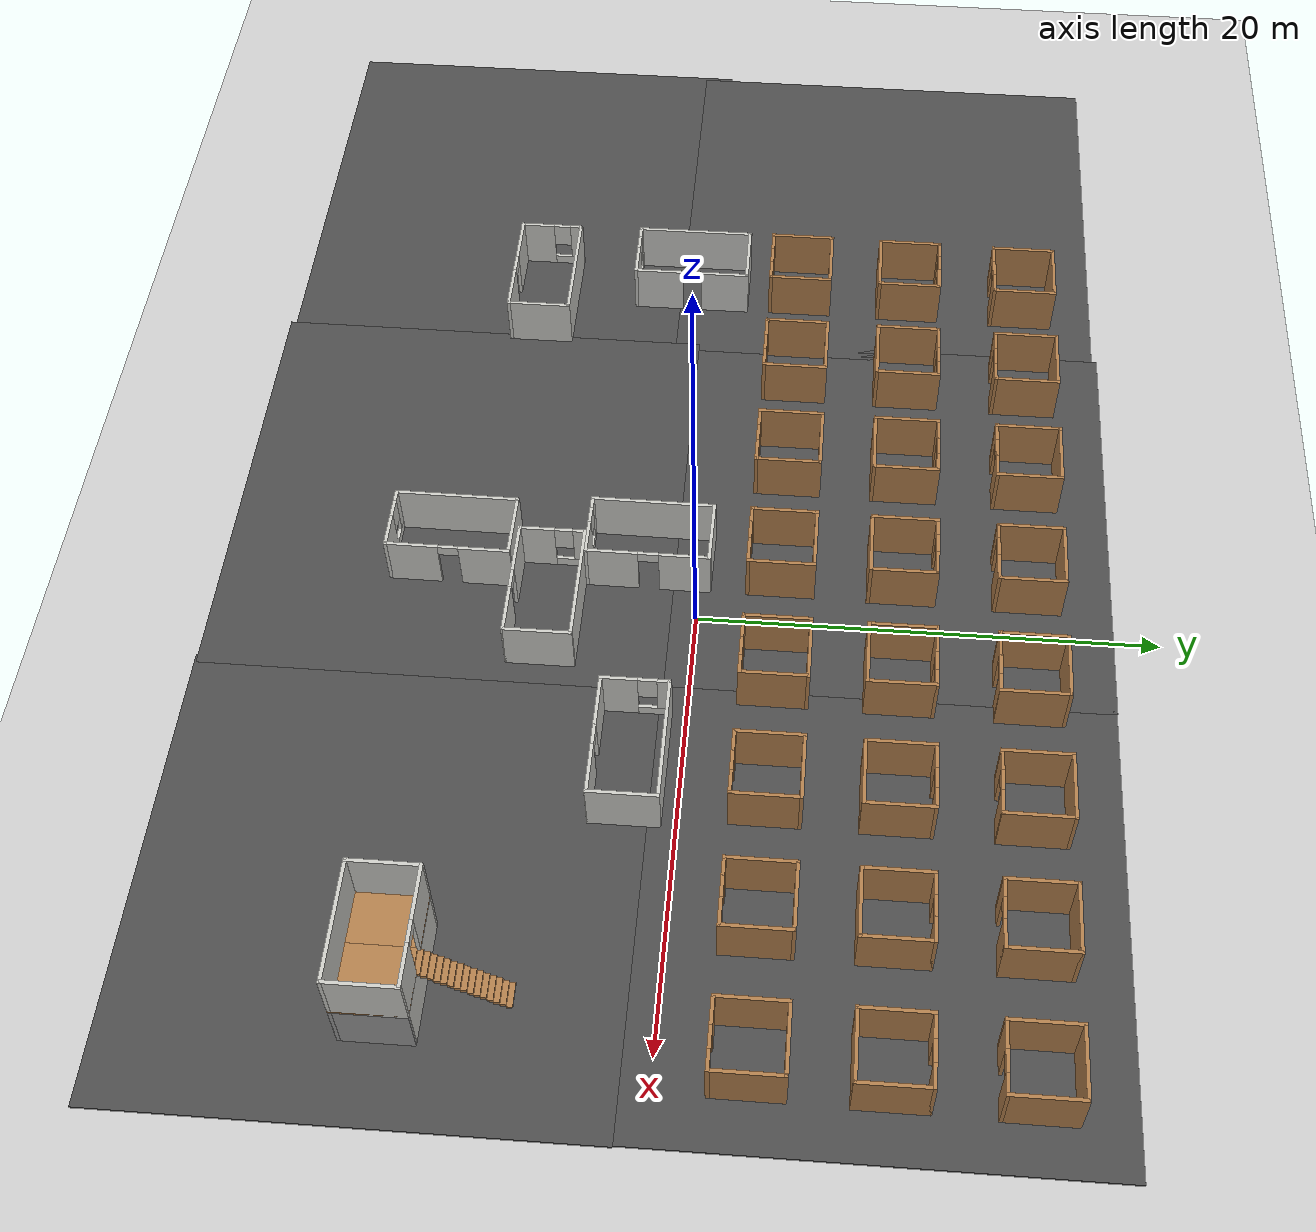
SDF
<sdf version="1.6">
 <world name="default">
  <light name="sun" type="directional">
   <pose>0 0 10 0 -0 0</pose>
   <diffuse>0.8 0.8 0.8 1</diffuse>
   <specular>0.2 0.2 0.2 1</specular>
   <attenuation>
    <range>1000</range>
    <constant>0.9</constant>
    <linear>0.01</linear>
    <quadratic>0.001</quadratic>
   </attenuation>
   <direction>-0.5 0.1 -0.9</direction>
  </light>
  <model name="ground_plane">
   <static>1</static>
   <link name="link">
    <collision name="collision">
     <geometry><plane><normal>0 0 1</normal><size>100 100</size></plane></geometry>
     <surface>
      <contact><collide_bitmask>65535</collide_bitmask></contact>
      <friction><ode><mu>100</mu><mu2>50</mu2></ode></friction>
     </surface>
    </collision>
    <visual name="visual">
     <cast_shadows>0</cast_shadows>
     <geometry><plane><normal>0 0 1</normal><size>100 100</size></plane></geometry>
     <material>
      <script><uri>file://media/materials/scripts/gazebo.material</uri><name>Gazebo/Grey</name></script>
     </material>
    </visual>
   </link>
  </model>
  <gravity>0 0 -9.8</gravity>
  <magnetic_field>6e-06 2.3e-05 -4.2e-05</magnetic_field>
  <atmosphere type="adiabatic"/>
  <physics name="default_physics" default="0" type="ode">
   <max_step_size>0.001</max_step_size>
   <real_time_factor>1</real_time_factor>
   <real_time_update_rate>0</real_time_update_rate>
  </physics>
  <scene><ambient>0.4 0.4 0.4 1</ambient><background>0.7 0.7 0.7 1</background><shadows>1</shadows></scene>
  <spherical_coordinates>
   <surface_model>EARTH_WGS84</surface_model>
   <latitude_deg>0</latitude_deg>
   <longitude_deg>0</longitude_deg>
   <elevation>0</elevation>
   <heading_deg>0</heading_deg>
  </spherical_coordinates>
  <model name="room_row_clone_clone_0">
   <pose>-0.049292 3.57608 0 0 -0 3.14</pose>
   <link name="Wall_11">
    <collision name="Wall_11_Collision">
     <geometry><box><size>3 0.15 2.5</size></box></geometry>
     <pose>0 0 1.25 0 -0 0</pose>
    </collision>
    <visual name="Wall_11_Visual">
     <pose>0 0 1.25 0 -0 0</pose>
     <geometry><box><size>3 0.15 2.5</size></box></geometry>
     <material>
      <script><uri>file://media/materials/scripts/gazebo.material</uri><name>Gazebo/Wood</name></script>
      <ambient>1 1 1 1</ambient>
     </material>
     <meta><layer>0</layer></meta>
    </visual>
    <pose>1.425 0 0 0 -0 -1.5708</pose>
   </link>
   <link name="Wall_12">
    <collision name="Wall_12_Collision">
     <geometry><box><size>3 0.15 2.5</size></box></geometry>
     <pose>0 0 1.25 0 -0 0</pose>
    </collision>
    <visual name="Wall_12_Visual">
     <pose>0 0 1.25 0 -0 0</pose>
     <geometry><box><size>3 0.15 2.5</size></box></geometry>
     <material>
      <script><uri>file://media/materials/scripts/gazebo.material</uri><name>Gazebo/Wood</name></script>
      <ambient>1 1 1 1</ambient>
     </material>
     <meta><layer>0</layer></meta>
    </visual>
    <pose>2.85 -1.425 0 0 -0 0</pose>
   </link>
   <link name="Wall_13">
    <collision name="Wall_13_Collision">
     <geometry><box><size>3 0.15 2.5</size></box></geometry>
     <pose>0 0 1.25 0 -0 0</pose>
    </collision>
    <visual name="Wall_13_Visual">
     <pose>0 0 1.25 0 -0 0</pose>
     <geometry><box><size>3 0.15 2.5</size></box></geometry>
     <material>
      <script><uri>file://media/materials/scripts/gazebo.material</uri><name>Gazebo/Wood</name></script>
      <ambient>1 1 1 1</ambient>
     </material>
     <meta><layer>0</layer></meta>
    </visual>
    <pose>4.275 0 0 0 -0 1.5708</pose>
   </link>
   <link name="Wall_14">
    <pose>2.85 1.425 0 0 -0 3.14159</pose>
    <visual name="Wall_14_Visual_0">
     <pose>-1.10207 0 1.25 0 -0 0</pose>
     <geometry><box><size>0.795857 0.15 2.5</size></box></geometry>
     <material>
      <script><uri>file://media/materials/scripts/gazebo.material</uri><name>Gazebo/Wood</name></script>
      <ambient>1 1 1 1</ambient>
     </material>
     <meta><layer>0</layer></meta>
    </visual>
    <collision name="Wall_14_Collision_0">
     <geometry><box><size>0.795857 0.15 2.5</size></box></geometry>
     <pose>-1.10207 0 1.25 0 -0 0</pose>
    </collision>
    <visual name="Wall_14_Visual_1">
     <pose>0.847928 0 1.25 0 -0 0</pose>
     <geometry><box><size>1.30414 0.15 2.5</size></box></geometry>
     <material>
      <script><uri>file://media/materials/scripts/gazebo.material</uri><name>Gazebo/Wood</name></script>
      <ambient>1 1 1 1</ambient>
     </material>
     <meta><layer>0</layer></meta>
    </visual>
    <collision name="Wall_14_Collision_1">
     <geometry><box><size>1.30414 0.15 2.5</size></box></geometry>
     <pose>0.847928 0 1.25 0 -0 0</pose>
    </collision>
    <visual name="Wall_14_Visual_2">
     <pose>-0.254143 0 2.25 0 -0 0</pose>
     <geometry><box><size>0.9 0.15 0.5</size></box></geometry>
     <material>
      <script><uri>file://media/materials/scripts/gazebo.material</uri><name>Gazebo/Wood</name></script>
      <ambient>1 1 1 1</ambient>
     </material>
     <meta><layer>0</layer></meta>
    </visual>
    <collision name="Wall_14_Collision_2">
     <geometry><box><size>0.9 0.15 0.5</size></box></geometry>
     <pose>-0.254143 0 2.25 0 -0 0</pose>
    </collision>
   </link>
   <link name="Wall_17">
    <collision name="Wall_17_Collision">
     <geometry><box><size>3 0.15 2.5</size></box></geometry>
     <pose>0 0 1.25 0 -0 0</pose>
    </collision>
    <visual name="Wall_17_Visual">
     <pose>0 0 1.25 0 -0 0</pose>
     <geometry><box><size>3 0.15 2.5</size></box></geometry>
     <material>
      <script><uri>file://media/materials/scripts/gazebo.material</uri><name>Gazebo/Wood</name></script>
      <ambient>1 1 1 1</ambient>
     </material>
     <meta><layer>0</layer></meta>
    </visual>
    <pose>7.125 0 0 0 -0 -1.5708</pose>
   </link>
   <link name="Wall_18">
    <collision name="Wall_18_Collision">
     <geometry><box><size>3 0.15 2.5</size></box></geometry>
     <pose>0 0 1.25 0 -0 0</pose>
    </collision>
    <visual name="Wall_18_Visual">
     <pose>0 0 1.25 0 -0 0</pose>
     <geometry><box><size>3 0.15 2.5</size></box></geometry>
     <material>
      <script><uri>file://media/materials/scripts/gazebo.material</uri><name>Gazebo/Wood</name></script>
      <ambient>1 1 1 1</ambient>
     </material>
     <meta><layer>0</layer></meta>
    </visual>
    <pose>8.55 -1.425 0 0 -0 0</pose>
   </link>
   <link name="Wall_19">
    <collision name="Wall_19_Collision">
     <geometry><box><size>3 0.15 2.5</size></box></geometry>
     <pose>0 0 1.25 0 -0 0</pose>
    </collision>
    <visual name="Wall_19_Visual">
     <pose>0 0 1.25 0 -0 0</pose>
     <geometry><box><size>3 0.15 2.5</size></box></geometry>
     <material>
      <script><uri>file://media/materials/scripts/gazebo.material</uri><name>Gazebo/Wood</name></script>
      <ambient>1 1 1 1</ambient>
     </material>
     <meta><layer>0</layer></meta>
    </visual>
    <pose>9.975 0 0 0 -0 1.5708</pose>
   </link>
   <link name="Wall_20">
    <pose>8.55 1.425 0 0 -0 3.14159</pose>
    <visual name="Wall_20_Visual_0">
     <pose>-1.03119 0 1.25 0 -0 0</pose>
     <geometry><box><size>0.937612 0.15 2.5</size></box></geometry>
     <material>
      <script><uri>file://media/materials/scripts/gazebo.material</uri><name>Gazebo/Wood</name></script>
      <ambient>1 1 1 1</ambient>
     </material>
     <meta><layer>0</layer></meta>
    </visual>
    <collision name="Wall_20_Collision_0">
     <geometry><box><size>0.937612 0.15 2.5</size></box></geometry>
     <pose>-1.03119 0 1.25 0 -0 0</pose>
    </collision>
    <visual name="Wall_20_Visual_1">
     <pose>0.918806 0 1.25 0 -0 0</pose>
     <geometry><box><size>1.16239 0.15 2.5</size></box></geometry>
     <material>
      <script><uri>file://media/materials/scripts/gazebo.material</uri><name>Gazebo/Wood</name></script>
      <ambient>1 1 1 1</ambient>
     </material>
     <meta><layer>0</layer></meta>
    </visual>
    <collision name="Wall_20_Collision_1">
     <geometry><box><size>1.16239 0.15 2.5</size></box></geometry>
     <pose>0.918806 0 1.25 0 -0 0</pose>
    </collision>
    <visual name="Wall_20_Visual_2">
     <pose>-0.112388 0 2.25 0 -0 0</pose>
     <geometry><box><size>0.9 0.15 0.5</size></box></geometry>
     <material>
      <script><uri>file://media/materials/scripts/gazebo.material</uri><name>Gazebo/Wood</name></script>
      <ambient>1 1 1 1</ambient>
     </material>
     <meta><layer>0</layer></meta>
    </visual>
    <collision name="Wall_20_Collision_2">
     <geometry><box><size>0.9 0.15 0.5</size></box></geometry>
     <pose>-0.112388 0 2.25 0 -0 0</pose>
    </collision>
   </link>
   <link name="Wall_23">
    <collision name="Wall_23_Collision">
     <geometry><box><size>3 0.15 2.5</size></box></geometry>
     <pose>0 0 1.25 0 -0 0</pose>
    </collision>
    <visual name="Wall_23_Visual">
     <pose>0 0 1.25 0 -0 0</pose>
     <geometry><box><size>3 0.15 2.5</size></box></geometry>
     <material>
      <script><uri>file://media/materials/scripts/gazebo.material</uri><name>Gazebo/Wood</name></script>
      <ambient>1 1 1 1</ambient>
     </material>
     <meta><layer>0</layer></meta>
    </visual>
    <pose>-7.125 0 0 0 -0 -1.5708</pose>
   </link>
   <link name="Wall_24">
    <collision name="Wall_24_Collision">
     <geometry><box><size>3 0.15 2.5</size></box></geometry>
     <pose>0 0 1.25 0 -0 0</pose>
    </collision>
    <visual name="Wall_24_Visual">
     <pose>0 0 1.25 0 -0 0</pose>
     <geometry><box><size>3 0.15 2.5</size></box></geometry>
     <material>
      <script><uri>file://media/materials/scripts/gazebo.material</uri><name>Gazebo/Wood</name></script>
      <ambient>1 1 1 1</ambient>
     </material>
     <meta><layer>0</layer></meta>
    </visual>
    <pose>-8.55 -1.425 0 0 -0 3.14159</pose>
   </link>
   <link name="Wall_25">
    <collision name="Wall_25_Collision">
     <geometry><box><size>3 0.15 2.5</size></box></geometry>
     <pose>0 0 1.25 0 -0 0</pose>
    </collision>
    <visual name="Wall_25_Visual">
     <pose>0 0 1.25 0 -0 0</pose>
     <geometry><box><size>3 0.15 2.5</size></box></geometry>
     <material>
      <script><uri>file://media/materials/scripts/gazebo.material</uri><name>Gazebo/Wood</name></script>
      <ambient>1 1 1 1</ambient>
     </material>
     <meta><layer>0</layer></meta>
    </visual>
    <pose>-9.975 0 0 0 -0 1.5708</pose>
   </link>
   <link name="Wall_26">
    <pose>-8.55 1.425 0 0 -0 0</pose>
    <visual name="Wall_26_Visual_0">
     <pose>-0.952424 0 1.25 0 -0 0</pose>
     <geometry><box><size>1.09515 0.15 2.5</size></box></geometry>
     <material>
      <script><uri>file://media/materials/scripts/gazebo.material</uri><name>Gazebo/Wood</name></script>
      <ambient>1 1 1 1</ambient>
     </material>
     <meta><layer>0</layer></meta>
    </visual>
    <collision name="Wall_26_Collision_0">
     <geometry><box><size>1.09515 0.15 2.5</size></box></geometry>
     <pose>-0.952424 0 1.25 0 -0 0</pose>
    </collision>
    <visual name="Wall_26_Visual_1">
     <pose>0.997576 0 1.25 0 -0 0</pose>
     <geometry><box><size>1.00485 0.15 2.5</size></box></geometry>
     <material>
      <script><uri>file://media/materials/scripts/gazebo.material</uri><name>Gazebo/Wood</name></script>
      <ambient>1 1 1 1</ambient>
     </material>
     <meta><layer>0</layer></meta>
    </visual>
    <collision name="Wall_26_Collision_1">
     <geometry><box><size>1.00485 0.15 2.5</size></box></geometry>
     <pose>0.997576 0 1.25 0 -0 0</pose>
    </collision>
    <visual name="Wall_26_Visual_2">
     <pose>0.045152 0 2.25 0 -0 0</pose>
     <geometry><box><size>0.9 0.15 0.5</size></box></geometry>
     <material>
      <script><uri>file://media/materials/scripts/gazebo.material</uri><name>Gazebo/Wood</name></script>
      <ambient>1 1 1 1</ambient>
     </material>
     <meta><layer>0</layer></meta>
    </visual>
    <collision name="Wall_26_Collision_2">
     <geometry><box><size>0.9 0.15 0.5</size></box></geometry>
     <pose>0.045152 0 2.25 0 -0 0</pose>
    </collision>
   </link>
   <link name="Wall_29">
    <collision name="Wall_29_Collision">
     <geometry><box><size>3 0.15 2.5</size></box></geometry>
     <pose>0 0 1.25 0 -0 0</pose>
    </collision>
    <visual name="Wall_29_Visual">
     <pose>0 0 1.25 0 -0 0</pose>
     <geometry><box><size>3 0.15 2.5</size></box></geometry>
     <material>
      <script><uri>file://media/materials/scripts/gazebo.material</uri><name>Gazebo/Wood</name></script>
      <ambient>1 1 1 1</ambient>
     </material>
     <meta><layer>0</layer></meta>
    </visual>
    <pose>-12.825 0 0 0 -0 -1.5708</pose>
   </link>
   <link name="Wall_30">
    <collision name="Wall_30_Collision">
     <geometry><box><size>3 0.15 2.5</size></box></geometry>
     <pose>0 0 1.25 0 -0 0</pose>
    </collision>
    <visual name="Wall_30_Visual">
     <pose>0 0 1.25 0 -0 0</pose>
     <geometry><box><size>3 0.15 2.5</size></box></geometry>
     <material>
      <script><uri>file://media/materials/scripts/gazebo.material</uri><name>Gazebo/Wood</name></script>
      <ambient>1 1 1 1</ambient>
     </material>
     <meta><layer>0</layer></meta>
    </visual>
    <pose>-14.25 -1.425 0 0 -0 3.14159</pose>
   </link>
   <link name="Wall_31">
    <collision name="Wall_31_Collision">
     <geometry><box><size>3 0.15 2.5</size></box></geometry>
     <pose>0 0 1.25 0 -0 0</pose>
    </collision>
    <visual name="Wall_31_Visual">
     <pose>0 0 1.25 0 -0 0</pose>
     <geometry><box><size>3 0.15 2.5</size></box></geometry>
     <material>
      <script><uri>file://media/materials/scripts/gazebo.material</uri><name>Gazebo/Wood</name></script>
      <ambient>1 1 1 1</ambient>
     </material>
     <meta><layer>0</layer></meta>
    </visual>
    <pose>-15.675 0 0 0 -0 1.5708</pose>
   </link>
   <link name="Wall_32">
    <pose>-14.25 1.425 0 0 -0 0</pose>
    <visual name="Wall_32_Visual_0">
     <pose>-0.881547 0 1.25 0 -0 0</pose>
     <geometry><box><size>1.23691 0.15 2.5</size></box></geometry>
     <material>
      <script><uri>file://media/materials/scripts/gazebo.material</uri><name>Gazebo/Wood</name></script>
      <ambient>1 1 1 1</ambient>
     </material>
     <meta><layer>0</layer></meta>
    </visual>
    <collision name="Wall_32_Collision_0">
     <geometry><box><size>1.23691 0.15 2.5</size></box></geometry>
     <pose>-0.881547 0 1.25 0 -0 0</pose>
    </collision>
    <visual name="Wall_32_Visual_1">
     <pose>1.06845 0 1.25 0 -0 0</pose>
     <geometry><box><size>0.863093 0.15 2.5</size></box></geometry>
     <material>
      <script><uri>file://media/materials/scripts/gazebo.material</uri><name>Gazebo/Wood</name></script>
      <ambient>1 1 1 1</ambient>
     </material>
     <meta><layer>0</layer></meta>
    </visual>
    <collision name="Wall_32_Collision_1">
     <geometry><box><size>0.863093 0.15 2.5</size></box></geometry>
     <pose>1.06845 0 1.25 0 -0 0</pose>
    </collision>
    <visual name="Wall_32_Visual_2">
     <pose>0.186907 0 2.25 0 -0 0</pose>
     <geometry><box><size>0.9 0.15 0.5</size></box></geometry>
     <material>
      <script><uri>file://media/materials/scripts/gazebo.material</uri><name>Gazebo/Wood</name></script>
      <ambient>1 1 1 1</ambient>
     </material>
     <meta><layer>0</layer></meta>
    </visual>
    <collision name="Wall_32_Collision_2">
     <geometry><box><size>0.9 0.15 0.5</size></box></geometry>
     <pose>0.186907 0 2.25 0 -0 0</pose>
    </collision>
   </link>
   <link name="Wall_35">
    <collision name="Wall_35_Collision">
     <geometry><box><size>3 0.15 2.5</size></box></geometry>
     <pose>0 0 1.25 0 -0 0</pose>
    </collision>
    <visual name="Wall_35_Visual">
     <pose>0 0 1.25 0 -0 0</pose>
     <geometry><box><size>3 0.15 2.5</size></box></geometry>
     <material>
      <script><uri>file://media/materials/scripts/gazebo.material</uri><name>Gazebo/Wood</name></script>
      <ambient>1 1 1 1</ambient>
     </material>
     <meta><layer>0</layer></meta>
    </visual>
    <pose>12.825 0 0 0 -0 -1.5708</pose>
   </link>
   <link name="Wall_36">
    <collision name="Wall_36_Collision">
     <geometry><box><size>3 0.15 2.5</size></box></geometry>
     <pose>0 0 1.25 0 -0 0</pose>
    </collision>
    <visual name="Wall_36_Visual">
     <pose>0 0 1.25 0 -0 0</pose>
     <geometry><box><size>3 0.15 2.5</size></box></geometry>
     <material>
      <script><uri>file://media/materials/scripts/gazebo.material</uri><name>Gazebo/Wood</name></script>
      <ambient>1 1 1 1</ambient>
     </material>
     <meta><layer>0</layer></meta>
    </visual>
    <pose>14.25 -1.425 0 0 -0 0</pose>
   </link>
   <link name="Wall_37">
    <collision name="Wall_37_Collision">
     <geometry><box><size>3 0.15 2.5</size></box></geometry>
     <pose>0 0 1.25 0 -0 0</pose>
    </collision>
    <visual name="Wall_37_Visual">
     <pose>0 0 1.25 0 -0 0</pose>
     <geometry><box><size>3 0.15 2.5</size></box></geometry>
     <material>
      <script><uri>file://media/materials/scripts/gazebo.material</uri><name>Gazebo/Wood</name></script>
      <ambient>1 1 1 1</ambient>
     </material>
     <meta><layer>0</layer></meta>
    </visual>
    <pose>15.675 0 0 0 -0 1.5708</pose>
   </link>
   <link name="Wall_38">
    <pose>14.25 1.425 0 0 -0 3.14159</pose>
    <visual name="Wall_38_Visual_0">
     <pose>-0.960316 0 1.25 0 -0 0</pose>
     <geometry><box><size>1.07937 0.15 2.5</size></box></geometry>
     <material>
      <script><uri>file://media/materials/scripts/gazebo.material</uri><name>Gazebo/Wood</name></script>
      <ambient>1 1 1 1</ambient>
     </material>
     <meta><layer>0</layer></meta>
    </visual>
    <collision name="Wall_38_Collision_0">
     <geometry><box><size>1.07937 0.15 2.5</size></box></geometry>
     <pose>-0.960316 0 1.25 0 -0 0</pose>
    </collision>
    <visual name="Wall_38_Visual_1">
     <pose>0.989684 0 1.25 0 -0 0</pose>
     <geometry><box><size>1.02063 0.15 2.5</size></box></geometry>
     <material>
      <script><uri>file://media/materials/scripts/gazebo.material</uri><name>Gazebo/Wood</name></script>
      <ambient>1 1 1 1</ambient>
     </material>
     <meta><layer>0</layer></meta>
    </visual>
    <collision name="Wall_38_Collision_1">
     <geometry><box><size>1.02063 0.15 2.5</size></box></geometry>
     <pose>0.989684 0 1.25 0 -0 0</pose>
    </collision>
    <visual name="Wall_38_Visual_2">
     <pose>0.029367 0 2.25 0 -0 0</pose>
     <geometry><box><size>0.9 0.15 0.5</size></box></geometry>
     <material>
      <script><uri>file://media/materials/scripts/gazebo.material</uri><name>Gazebo/Wood</name></script>
      <ambient>1 1 1 1</ambient>
     </material>
     <meta><layer>0</layer></meta>
    </visual>
    <collision name="Wall_38_Collision_2">
     <geometry><box><size>0.9 0.15 0.5</size></box></geometry>
     <pose>0.029367 0 2.25 0 -0 0</pose>
    </collision>
   </link>
   <link name="Wall_41">
    <collision name="Wall_41_Collision">
     <geometry><box><size>3 0.15 2.5</size></box></geometry>
     <pose>0 0 1.25 0 -0 0</pose>
    </collision>
    <visual name="Wall_41_Visual">
     <pose>0 0 1.25 0 -0 0</pose>
     <geometry><box><size>3 0.15 2.5</size></box></geometry>
     <material>
      <script><uri>file://media/materials/scripts/gazebo.material</uri><name>Gazebo/Wood</name></script>
      <ambient>1 1 1 1</ambient>
     </material>
     <meta><layer>0</layer></meta>
    </visual>
    <pose>-18.525 0 0 0 -0 -1.5708</pose>
   </link>
   <link name="Wall_42">
    <collision name="Wall_42_Collision">
     <geometry><box><size>3 0.15 2.5</size></box></geometry>
     <pose>0 0 1.25 0 -0 0</pose>
    </collision>
    <visual name="Wall_42_Visual">
     <pose>0 0 1.25 0 -0 0</pose>
     <geometry><box><size>3 0.15 2.5</size></box></geometry>
     <material>
      <script><uri>file://media/materials/scripts/gazebo.material</uri><name>Gazebo/Wood</name></script>
      <ambient>1 1 1 1</ambient>
     </material>
     <meta><layer>0</layer></meta>
    </visual>
    <pose>-19.95 -1.425 0 0 -0 3.14159</pose>
   </link>
   <link name="Wall_45">
    <pose>-19.95 1.425 0 0 -0 3.14159</pose>
    <visual name="Wall_45_Visual_0">
     <pose>-0.89308 0 1.25 0 -0 0</pose>
     <geometry><box><size>1.21384 0.15 2.5</size></box></geometry>
     <material>
      <script><uri>file://media/materials/scripts/gazebo.material</uri><name>Gazebo/Wood</name></script>
      <ambient>1 1 1 1</ambient>
     </material>
     <meta><layer>0</layer></meta>
    </visual>
    <collision name="Wall_45_Collision_0">
     <geometry><box><size>1.21384 0.15 2.5</size></box></geometry>
     <pose>-0.89308 0 1.25 0 -0 0</pose>
    </collision>
    <visual name="Wall_45_Visual_1">
     <pose>1.05692 0 1.25 0 -0 0</pose>
     <geometry><box><size>0.886161 0.15 2.5</size></box></geometry>
     <material>
      <script><uri>file://media/materials/scripts/gazebo.material</uri><name>Gazebo/Wood</name></script>
      <ambient>1 1 1 1</ambient>
     </material>
     <meta><layer>0</layer></meta>
    </visual>
    <collision name="Wall_45_Collision_1">
     <geometry><box><size>0.886161 0.15 2.5</size></box></geometry>
     <pose>1.05692 0 1.25 0 -0 0</pose>
    </collision>
    <visual name="Wall_45_Visual_2">
     <pose>0.163839 0 2.25 0 -0 0</pose>
     <geometry><box><size>0.9 0.15 0.5</size></box></geometry>
     <material>
      <script><uri>file://media/materials/scripts/gazebo.material</uri><name>Gazebo/Wood</name></script>
      <ambient>1 1 1 1</ambient>
     </material>
     <meta><layer>0</layer></meta>
    </visual>
    <collision name="Wall_45_Collision_2">
     <geometry><box><size>0.9 0.15 0.5</size></box></geometry>
     <pose>0.163839 0 2.25 0 -0 0</pose>
    </collision>
   </link>
   <link name="Wall_46">
    <collision name="Wall_46_Collision">
     <geometry><box><size>3 0.15 2.5</size></box></geometry>
     <pose>0 0 1.25 0 -0 0</pose>
    </collision>
    <visual name="Wall_46_Visual">
     <pose>0 0 1.25 0 -0 0</pose>
     <geometry><box><size>3 0.15 2.5</size></box></geometry>
     <material>
      <script><uri>file://media/materials/scripts/gazebo.material</uri><name>Gazebo/Wood</name></script>
      <ambient>1 1 1 1</ambient>
     </material>
     <meta><layer>0</layer></meta>
    </visual>
    <pose>-21.375 0 0 0 -0 -1.5708</pose>
   </link>
   <link name="Wall_49">
    <collision name="Wall_49_Collision">
     <geometry><box><size>3 0.15 2.5</size></box></geometry>
     <pose>0 0 1.25 0 -0 0</pose>
    </collision>
    <visual name="Wall_49_Visual">
     <pose>0 0 1.25 0 -0 0</pose>
     <geometry><box><size>3 0.15 2.5</size></box></geometry>
     <material>
      <script><uri>file://media/materials/scripts/gazebo.material</uri><name>Gazebo/Wood</name></script>
      <ambient>1 1 1 1</ambient>
     </material>
     <meta><layer>0</layer></meta>
    </visual>
    <pose>18.525 0 0 0 -0 -1.5708</pose>
   </link>
   <link name="Wall_5">
    <pose>-2.85 1.425 0 0 -0 0</pose>
    <visual name="Wall_5_Visual_0">
     <pose>-1.05848 0 1.25 0 -0 0</pose>
     <geometry><box><size>0.883039 0.15 2.5</size></box></geometry>
     <material>
      <script><uri>file://media/materials/scripts/gazebo.material</uri><name>Gazebo/Wood</name></script>
      <ambient>1 1 1 1</ambient>
     </material>
     <meta><layer>0</layer></meta>
    </visual>
    <collision name="Wall_5_Collision_0">
     <geometry><box><size>0.883039 0.15 2.5</size></box></geometry>
     <pose>-1.05848 0 1.25 0 -0 0</pose>
    </collision>
    <visual name="Wall_5_Visual_1">
     <pose>0.891519 0 1.25 0 -0 0</pose>
     <geometry><box><size>1.21696 0.15 2.5</size></box></geometry>
     <material>
      <script><uri>file://media/materials/scripts/gazebo.material</uri><name>Gazebo/Wood</name></script>
      <ambient>1 1 1 1</ambient>
     </material>
     <meta><layer>0</layer></meta>
    </visual>
    <collision name="Wall_5_Collision_1">
     <geometry><box><size>1.21696 0.15 2.5</size></box></geometry>
     <pose>0.891519 0 1.25 0 -0 0</pose>
    </collision>
    <visual name="Wall_5_Visual_2">
     <pose>-0.166961 0 2.25 0 -0 0</pose>
     <geometry><box><size>0.9 0.15 0.5</size></box></geometry>
     <material>
      <script><uri>file://media/materials/scripts/gazebo.material</uri><name>Gazebo/Wood</name></script>
      <ambient>1 1 1 1</ambient>
     </material>
     <meta><layer>0</layer></meta>
    </visual>
    <collision name="Wall_5_Collision_2">
     <geometry><box><size>0.9 0.15 0.5</size></box></geometry>
     <pose>-0.166961 0 2.25 0 -0 0</pose>
    </collision>
   </link>
   <link name="Wall_51">
    <collision name="Wall_51_Collision">
     <geometry><box><size>3 0.15 2.5</size></box></geometry>
     <pose>0 0 1.25 0 -0 0</pose>
    </collision>
    <visual name="Wall_51_Visual">
     <pose>0 0 1.25 0 -0 0</pose>
     <geometry><box><size>3 0.15 2.5</size></box></geometry>
     <material>
      <script><uri>file://media/materials/scripts/gazebo.material</uri><name>Gazebo/Wood</name></script>
      <ambient>1 1 1 1</ambient>
     </material>
     <meta><layer>0</layer></meta>
    </visual>
    <pose>19.95 -1.425 0 0 -0 0</pose>
   </link>
   <link name="Wall_53">
    <collision name="Wall_53_Collision">
     <geometry><box><size>3 0.15 2.5</size></box></geometry>
     <pose>0 0 1.25 0 -0 0</pose>
    </collision>
    <visual name="Wall_53_Visual">
     <pose>0 0 1.25 0 -0 0</pose>
     <geometry><box><size>3 0.15 2.5</size></box></geometry>
     <material>
      <script><uri>file://media/materials/scripts/gazebo.material</uri><name>Gazebo/Wood</name></script>
      <ambient>1 1 1 1</ambient>
     </material>
     <meta><layer>0</layer></meta>
    </visual>
    <pose>21.375 0 0 0 -0 1.5708</pose>
   </link>
   <link name="Wall_54">
    <pose>19.95 1.425 0 0 -0 3.14159</pose>
    <visual name="Wall_54_Visual_0">
     <pose>-0.994975 0 1.25 0 -0 0</pose>
     <geometry><box><size>1.01005 0.15 2.5</size></box></geometry>
     <material>
      <script><uri>file://media/materials/scripts/gazebo.material</uri><name>Gazebo/Wood</name></script>
      <ambient>1 1 1 1</ambient>
     </material>
     <meta><layer>0</layer></meta>
    </visual>
    <collision name="Wall_54_Collision_0">
     <geometry><box><size>1.01005 0.15 2.5</size></box></geometry>
     <pose>-0.994975 0 1.25 0 -0 0</pose>
    </collision>
    <visual name="Wall_54_Visual_1">
     <pose>0.955025 0 1.25 0 -0 0</pose>
     <geometry><box><size>1.08995 0.15 2.5</size></box></geometry>
     <material>
      <script><uri>file://media/materials/scripts/gazebo.material</uri><name>Gazebo/Wood</name></script>
      <ambient>1 1 1 1</ambient>
     </material>
     <meta><layer>0</layer></meta>
    </visual>
    <collision name="Wall_54_Collision_1">
     <geometry><box><size>1.08995 0.15 2.5</size></box></geometry>
     <pose>0.955025 0 1.25 0 -0 0</pose>
    </collision>
    <visual name="Wall_54_Visual_2">
     <pose>-0.039949 0 2.25 0 -0 0</pose>
     <geometry><box><size>0.9 0.15 0.5</size></box></geometry>
     <material>
      <script><uri>file://media/materials/scripts/gazebo.material</uri><name>Gazebo/Wood</name></script>
      <ambient>1 1 1 1</ambient>
     </material>
     <meta><layer>0</layer></meta>
    </visual>
    <collision name="Wall_54_Collision_2">
     <geometry><box><size>0.9 0.15 0.5</size></box></geometry>
     <pose>-0.039949 0 2.25 0 -0 0</pose>
    </collision>
   </link>
   <link name="Wall_6">
    <collision name="Wall_6_Collision">
     <geometry><box><size>3 0.15 2.5</size></box></geometry>
     <pose>0 0 1.25 0 -0 0</pose>
    </collision>
    <visual name="Wall_6_Visual">
     <pose>0 0 1.25 0 -0 0</pose>
     <geometry><box><size>3 0.15 2.5</size></box></geometry>
     <material>
      <script><uri>file://media/materials/scripts/gazebo.material</uri><name>Gazebo/Wood</name></script>
      <ambient>1 1 1 1</ambient>
     </material>
     <meta><layer>0</layer></meta>
    </visual>
    <pose>-1.425 0 0 0 -0 -1.5708</pose>
   </link>
   <link name="Wall_7">
    <collision name="Wall_7_Collision">
     <geometry><box><size>3 0.15 2.5</size></box></geometry>
     <pose>0 0 1.25 0 -0 0</pose>
    </collision>
    <visual name="Wall_7_Visual">
     <pose>0 0 1.25 0 -0 0</pose>
     <geometry><box><size>3 0.15 2.5</size></box></geometry>
     <material>
      <script><uri>file://media/materials/scripts/gazebo.material</uri><name>Gazebo/Wood</name></script>
      <ambient>1 1 1 1</ambient>
     </material>
     <meta><layer>0</layer></meta>
    </visual>
    <pose>-2.85 -1.425 0 0 -0 3.14159</pose>
   </link>
   <link name="Wall_8">
    <collision name="Wall_8_Collision">
     <geometry><box><size>3 0.15 2.5</size></box></geometry>
     <pose>0 0 1.25 0 -0 0</pose>
    </collision>
    <visual name="Wall_8_Visual">
     <pose>0 0 1.25 0 -0 0</pose>
     <geometry><box><size>3 0.15 2.5</size></box></geometry>
     <material>
      <script><uri>file://media/materials/scripts/gazebo.material</uri><name>Gazebo/Wood</name></script>
      <ambient>1 1 1 1</ambient>
     </material>
     <meta><layer>0</layer></meta>
    </visual>
    <pose>-4.275 0 0 0 -0 1.5708</pose>
   </link>
   <static>1</static>
  </model>
  <model name="room_row_clone_clone_1">
   <pose>-0.00322 8.84362 0 0 -0 0</pose>
   <link name="Wall_11">
    <collision name="Wall_11_Collision">
     <geometry><box><size>3 0.15 2.5</size></box></geometry>
     <pose>0 0 1.25 0 -0 0</pose>
    </collision>
    <visual name="Wall_11_Visual">
     <pose>0 0 1.25 0 -0 0</pose>
     <geometry><box><size>3 0.15 2.5</size></box></geometry>
     <material>
      <script><uri>file://media/materials/scripts/gazebo.material</uri><name>Gazebo/Wood</name></script>
      <ambient>1 1 1 1</ambient>
     </material>
     <meta><layer>0</layer></meta>
    </visual>
    <pose>1.425 0 0 0 -0 -1.5708</pose>
   </link>
   <link name="Wall_12">
    <collision name="Wall_12_Collision">
     <geometry><box><size>3 0.15 2.5</size></box></geometry>
     <pose>0 0 1.25 0 -0 0</pose>
    </collision>
    <visual name="Wall_12_Visual">
     <pose>0 0 1.25 0 -0 0</pose>
     <geometry><box><size>3 0.15 2.5</size></box></geometry>
     <material>
      <script><uri>file://media/materials/scripts/gazebo.material</uri><name>Gazebo/Wood</name></script>
      <ambient>1 1 1 1</ambient>
     </material>
     <meta><layer>0</layer></meta>
    </visual>
    <pose>2.85 -1.425 0 0 -0 0</pose>
   </link>
   <link name="Wall_13">
    <collision name="Wall_13_Collision">
     <geometry><box><size>3 0.15 2.5</size></box></geometry>
     <pose>0 0 1.25 0 -0 0</pose>
    </collision>
    <visual name="Wall_13_Visual">
     <pose>0 0 1.25 0 -0 0</pose>
     <geometry><box><size>3 0.15 2.5</size></box></geometry>
     <material>
      <script><uri>file://media/materials/scripts/gazebo.material</uri><name>Gazebo/Wood</name></script>
      <ambient>1 1 1 1</ambient>
     </material>
     <meta><layer>0</layer></meta>
    </visual>
    <pose>4.275 0 0 0 -0 1.5708</pose>
   </link>
   <link name="Wall_14">
    <pose>2.85 1.425 0 0 -0 3.14159</pose>
    <visual name="Wall_14_Visual_0">
     <pose>-1.10207 0 1.25 0 -0 0</pose>
     <geometry><box><size>0.795857 0.15 2.5</size></box></geometry>
     <material>
      <script><uri>file://media/materials/scripts/gazebo.material</uri><name>Gazebo/Wood</name></script>
      <ambient>1 1 1 1</ambient>
     </material>
     <meta><layer>0</layer></meta>
    </visual>
    <collision name="Wall_14_Collision_0">
     <geometry><box><size>0.795857 0.15 2.5</size></box></geometry>
     <pose>-1.10207 0 1.25 0 -0 0</pose>
    </collision>
    <visual name="Wall_14_Visual_1">
     <pose>0.847928 0 1.25 0 -0 0</pose>
     <geometry><box><size>1.30414 0.15 2.5</size></box></geometry>
     <material>
      <script><uri>file://media/materials/scripts/gazebo.material</uri><name>Gazebo/Wood</name></script>
      <ambient>1 1 1 1</ambient>
     </material>
     <meta><layer>0</layer></meta>
    </visual>
    <collision name="Wall_14_Collision_1">
     <geometry><box><size>1.30414 0.15 2.5</size></box></geometry>
     <pose>0.847928 0 1.25 0 -0 0</pose>
    </collision>
    <visual name="Wall_14_Visual_2">
     <pose>-0.254143 0 2.25 0 -0 0</pose>
     <geometry><box><size>0.9 0.15 0.5</size></box></geometry>
     <material>
      <script><uri>file://media/materials/scripts/gazebo.material</uri><name>Gazebo/Wood</name></script>
      <ambient>1 1 1 1</ambient>
     </material>
     <meta><layer>0</layer></meta>
    </visual>
    <collision name="Wall_14_Collision_2">
     <geometry><box><size>0.9 0.15 0.5</size></box></geometry>
     <pose>-0.254143 0 2.25 0 -0 0</pose>
    </collision>
   </link>
   <link name="Wall_17">
    <collision name="Wall_17_Collision">
     <geometry><box><size>3 0.15 2.5</size></box></geometry>
     <pose>0 0 1.25 0 -0 0</pose>
    </collision>
    <visual name="Wall_17_Visual">
     <pose>0 0 1.25 0 -0 0</pose>
     <geometry><box><size>3 0.15 2.5</size></box></geometry>
     <material>
      <script><uri>file://media/materials/scripts/gazebo.material</uri><name>Gazebo/Wood</name></script>
      <ambient>1 1 1 1</ambient>
     </material>
     <meta><layer>0</layer></meta>
    </visual>
    <pose>7.125 0 0 0 -0 -1.5708</pose>
   </link>
   <link name="Wall_18">
    <collision name="Wall_18_Collision">
     <geometry><box><size>3 0.15 2.5</size></box></geometry>
     <pose>0 0 1.25 0 -0 0</pose>
    </collision>
    <visual name="Wall_18_Visual">
     <pose>0 0 1.25 0 -0 0</pose>
     <geometry><box><size>3 0.15 2.5</size></box></geometry>
     <material>
      <script><uri>file://media/materials/scripts/gazebo.material</uri><name>Gazebo/Wood</name></script>
      <ambient>1 1 1 1</ambient>
     </material>
     <meta><layer>0</layer></meta>
    </visual>
    <pose>8.55 -1.425 0 0 -0 0</pose>
   </link>
   <link name="Wall_19">
    <collision name="Wall_19_Collision">
     <geometry><box><size>3 0.15 2.5</size></box></geometry>
     <pose>0 0 1.25 0 -0 0</pose>
    </collision>
    <visual name="Wall_19_Visual">
     <pose>0 0 1.25 0 -0 0</pose>
     <geometry><box><size>3 0.15 2.5</size></box></geometry>
     <material>
      <script><uri>file://media/materials/scripts/gazebo.material</uri><name>Gazebo/Wood</name></script>
      <ambient>1 1 1 1</ambient>
     </material>
     <meta><layer>0</layer></meta>
    </visual>
    <pose>9.975 0 0 0 -0 1.5708</pose>
   </link>
   <link name="Wall_20">
    <pose>8.55 1.425 0 0 -0 3.14159</pose>
    <visual name="Wall_20_Visual_0">
     <pose>-1.03119 0 1.25 0 -0 0</pose>
     <geometry><box><size>0.937612 0.15 2.5</size></box></geometry>
     <material>
      <script><uri>file://media/materials/scripts/gazebo.material</uri><name>Gazebo/Wood</name></script>
      <ambient>1 1 1 1</ambient>
     </material>
     <meta><layer>0</layer></meta>
    </visual>
    <collision name="Wall_20_Collision_0">
     <geometry><box><size>0.937612 0.15 2.5</size></box></geometry>
     <pose>-1.03119 0 1.25 0 -0 0</pose>
    </collision>
    <visual name="Wall_20_Visual_1">
     <pose>0.918806 0 1.25 0 -0 0</pose>
     <geometry><box><size>1.16239 0.15 2.5</size></box></geometry>
     <material>
      <script><uri>file://media/materials/scripts/gazebo.material</uri><name>Gazebo/Wood</name></script>
      <ambient>1 1 1 1</ambient>
     </material>
     <meta><layer>0</layer></meta>
    </visual>
    <collision name="Wall_20_Collision_1">
     <geometry><box><size>1.16239 0.15 2.5</size></box></geometry>
     <pose>0.918806 0 1.25 0 -0 0</pose>
    </collision>
    <visual name="Wall_20_Visual_2">
     <pose>-0.112388 0 2.25 0 -0 0</pose>
     <geometry><box><size>0.9 0.15 0.5</size></box></geometry>
     <material>
      <script><uri>file://media/materials/scripts/gazebo.material</uri><name>Gazebo/Wood</name></script>
      <ambient>1 1 1 1</ambient>
     </material>
     <meta><layer>0</layer></meta>
    </visual>
    <collision name="Wall_20_Collision_2">
     <geometry><box><size>0.9 0.15 0.5</size></box></geometry>
     <pose>-0.112388 0 2.25 0 -0 0</pose>
    </collision>
   </link>
   <link name="Wall_23">
    <collision name="Wall_23_Collision">
     <geometry><box><size>3 0.15 2.5</size></box></geometry>
     <pose>0 0 1.25 0 -0 0</pose>
    </collision>
    <visual name="Wall_23_Visual">
     <pose>0 0 1.25 0 -0 0</pose>
     <geometry><box><size>3 0.15 2.5</size></box></geometry>
     <material>
      <script><uri>file://media/materials/scripts/gazebo.material</uri><name>Gazebo/Wood</name></script>
      <ambient>1 1 1 1</ambient>
     </material>
     <meta><layer>0</layer></meta>
    </visual>
    <pose>-7.125 0 0 0 -0 -1.5708</pose>
   </link>
   <link name="Wall_24">
    <collision name="Wall_24_Collision">
     <geometry><box><size>3 0.15 2.5</size></box></geometry>
     <pose>0 0 1.25 0 -0 0</pose>
    </collision>
    <visual name="Wall_24_Visual">
     <pose>0 0 1.25 0 -0 0</pose>
     <geometry><box><size>3 0.15 2.5</size></box></geometry>
     <material>
      <script><uri>file://media/materials/scripts/gazebo.material</uri><name>Gazebo/Wood</name></script>
      <ambient>1 1 1 1</ambient>
     </material>
     <meta><layer>0</layer></meta>
    </visual>
    <pose>-8.55 -1.425 0 0 -0 3.14159</pose>
   </link>
   <link name="Wall_25">
    <collision name="Wall_25_Collision">
     <geometry><box><size>3 0.15 2.5</size></box></geometry>
     <pose>0 0 1.25 0 -0 0</pose>
    </collision>
    <visual name="Wall_25_Visual">
     <pose>0 0 1.25 0 -0 0</pose>
     <geometry><box><size>3 0.15 2.5</size></box></geometry>
     <material>
      <script><uri>file://media/materials/scripts/gazebo.material</uri><name>Gazebo/Wood</name></script>
      <ambient>1 1 1 1</ambient>
     </material>
     <meta><layer>0</layer></meta>
    </visual>
    <pose>-9.975 0 0 0 -0 1.5708</pose>
   </link>
   <link name="Wall_26">
    <pose>-8.55 1.425 0 0 -0 0</pose>
    <visual name="Wall_26_Visual_0">
     <pose>-0.952424 0 1.25 0 -0 0</pose>
     <geometry><box><size>1.09515 0.15 2.5</size></box></geometry>
     <material>
      <script><uri>file://media/materials/scripts/gazebo.material</uri><name>Gazebo/Wood</name></script>
      <ambient>1 1 1 1</ambient>
     </material>
     <meta><layer>0</layer></meta>
    </visual>
    <collision name="Wall_26_Collision_0">
     <geometry><box><size>1.09515 0.15 2.5</size></box></geometry>
     <pose>-0.952424 0 1.25 0 -0 0</pose>
    </collision>
    <visual name="Wall_26_Visual_1">
     <pose>0.997576 0 1.25 0 -0 0</pose>
     <geometry><box><size>1.00485 0.15 2.5</size></box></geometry>
     <material>
      <script><uri>file://media/materials/scripts/gazebo.material</uri><name>Gazebo/Wood</name></script>
      <ambient>1 1 1 1</ambient>
     </material>
     <meta><layer>0</layer></meta>
    </visual>
    <collision name="Wall_26_Collision_1">
     <geometry><box><size>1.00485 0.15 2.5</size></box></geometry>
     <pose>0.997576 0 1.25 0 -0 0</pose>
    </collision>
    <visual name="Wall_26_Visual_2">
     <pose>0.045152 0 2.25 0 -0 0</pose>
     <geometry><box><size>0.9 0.15 0.5</size></box></geometry>
     <material>
      <script><uri>file://media/materials/scripts/gazebo.material</uri><name>Gazebo/Wood</name></script>
      <ambient>1 1 1 1</ambient>
     </material>
     <meta><layer>0</layer></meta>
    </visual>
    <collision name="Wall_26_Collision_2">
     <geometry><box><size>0.9 0.15 0.5</size></box></geometry>
     <pose>0.045152 0 2.25 0 -0 0</pose>
    </collision>
   </link>
   <link name="Wall_29">
    <collision name="Wall_29_Collision">
     <geometry><box><size>3 0.15 2.5</size></box></geometry>
     <pose>0 0 1.25 0 -0 0</pose>
    </collision>
    <visual name="Wall_29_Visual">
     <pose>0 0 1.25 0 -0 0</pose>
     <geometry><box><size>3 0.15 2.5</size></box></geometry>
     <material>
      <script><uri>file://media/materials/scripts/gazebo.material</uri><name>Gazebo/Wood</name></script>
      <ambient>1 1 1 1</ambient>
     </material>
     <meta><layer>0</layer></meta>
    </visual>
    <pose>-12.825 0 0 0 -0 -1.5708</pose>
   </link>
   <link name="Wall_30">
    <collision name="Wall_30_Collision">
     <geometry><box><size>3 0.15 2.5</size></box></geometry>
     <pose>0 0 1.25 0 -0 0</pose>
    </collision>
    <visual name="Wall_30_Visual">
     <pose>0 0 1.25 0 -0 0</pose>
     <geometry><box><size>3 0.15 2.5</size></box></geometry>
     <material>
      <script><uri>file://media/materials/scripts/gazebo.material</uri><name>Gazebo/Wood</name></script>
      <ambient>1 1 1 1</ambient>
     </material>
     <meta><layer>0</layer></meta>
    </visual>
    <pose>-14.25 -1.425 0 0 -0 3.14159</pose>
   </link>
   <link name="Wall_31">
    <collision name="Wall_31_Collision">
     <geometry><box><size>3 0.15 2.5</size></box></geometry>
     <pose>0 0 1.25 0 -0 0</pose>
    </collision>
    <visual name="Wall_31_Visual">
     <pose>0 0 1.25 0 -0 0</pose>
     <geometry><box><size>3 0.15 2.5</size></box></geometry>
     <material>
      <script><uri>file://media/materials/scripts/gazebo.material</uri><name>Gazebo/Wood</name></script>
      <ambient>1 1 1 1</ambient>
     </material>
     <meta><layer>0</layer></meta>
    </visual>
    <pose>-15.675 0 0 0 -0 1.5708</pose>
   </link>
   <link name="Wall_32">
    <pose>-14.25 1.425 0 0 -0 0</pose>
    <visual name="Wall_32_Visual_0">
     <pose>-0.881547 0 1.25 0 -0 0</pose>
     <geometry><box><size>1.23691 0.15 2.5</size></box></geometry>
     <material>
      <script><uri>file://media/materials/scripts/gazebo.material</uri><name>Gazebo/Wood</name></script>
      <ambient>1 1 1 1</ambient>
     </material>
     <meta><layer>0</layer></meta>
    </visual>
    <collision name="Wall_32_Collision_0">
     <geometry><box><size>1.23691 0.15 2.5</size></box></geometry>
     <pose>-0.881547 0 1.25 0 -0 0</pose>
    </collision>
    <visual name="Wall_32_Visual_1">
     <pose>1.06845 0 1.25 0 -0 0</pose>
     <geometry><box><size>0.863093 0.15 2.5</size></box></geometry>
     <material>
      <script><uri>file://media/materials/scripts/gazebo.material</uri><name>Gazebo/Wood</name></script>
      <ambient>1 1 1 1</ambient>
     </material>
     <meta><layer>0</layer></meta>
    </visual>
    <collision name="Wall_32_Collision_1">
     <geometry><box><size>0.863093 0.15 2.5</size></box></geometry>
     <pose>1.06845 0 1.25 0 -0 0</pose>
    </collision>
    <visual name="Wall_32_Visual_2">
     <pose>0.186907 0 2.25 0 -0 0</pose>
     <geometry><box><size>0.9 0.15 0.5</size></box></geometry>
     <material>
      <script><uri>file://media/materials/scripts/gazebo.material</uri><name>Gazebo/Wood</name></script>
      <ambient>1 1 1 1</ambient>
     </material>
     <meta><layer>0</layer></meta>
    </visual>
    <collision name="Wall_32_Collision_2">
     <geometry><box><size>0.9 0.15 0.5</size></box></geometry>
     <pose>0.186907 0 2.25 0 -0 0</pose>
    </collision>
   </link>
   <link name="Wall_35">
    <collision name="Wall_35_Collision">
     <geometry><box><size>3 0.15 2.5</size></box></geometry>
     <pose>0 0 1.25 0 -0 0</pose>
    </collision>
    <visual name="Wall_35_Visual">
     <pose>0 0 1.25 0 -0 0</pose>
     <geometry><box><size>3 0.15 2.5</size></box></geometry>
     <material>
      <script><uri>file://media/materials/scripts/gazebo.material</uri><name>Gazebo/Wood</name></script>
      <ambient>1 1 1 1</ambient>
     </material>
     <meta><layer>0</layer></meta>
    </visual>
    <pose>12.825 0 0 0 -0 -1.5708</pose>
   </link>
   <link name="Wall_36">
    <collision name="Wall_36_Collision">
     <geometry><box><size>3 0.15 2.5</size></box></geometry>
     <pose>0 0 1.25 0 -0 0</pose>
    </collision>
    <visual name="Wall_36_Visual">
     <pose>0 0 1.25 0 -0 0</pose>
     <geometry><box><size>3 0.15 2.5</size></box></geometry>
     <material>
      <script><uri>file://media/materials/scripts/gazebo.material</uri><name>Gazebo/Wood</name></script>
      <ambient>1 1 1 1</ambient>
     </material>
     <meta><layer>0</layer></meta>
    </visual>
    <pose>14.25 -1.425 0 0 -0 0</pose>
   </link>
   <link name="Wall_37">
    <collision name="Wall_37_Collision">
     <geometry><box><size>3 0.15 2.5</size></box></geometry>
     <pose>0 0 1.25 0 -0 0</pose>
    </collision>
    <visual name="Wall_37_Visual">
     <pose>0 0 1.25 0 -0 0</pose>
     <geometry><box><size>3 0.15 2.5</size></box></geometry>
     <material>
      <script><uri>file://media/materials/scripts/gazebo.material</uri><name>Gazebo/Wood</name></script>
      <ambient>1 1 1 1</ambient>
     </material>
     <meta><layer>0</layer></meta>
    </visual>
    <pose>15.675 0 0 0 -0 1.5708</pose>
   </link>
   <link name="Wall_38">
    <pose>14.25 1.425 0 0 -0 3.14159</pose>
    <visual name="Wall_38_Visual_0">
     <pose>-0.960316 0 1.25 0 -0 0</pose>
     <geometry><box><size>1.07937 0.15 2.5</size></box></geometry>
     <material>
      <script><uri>file://media/materials/scripts/gazebo.material</uri><name>Gazebo/Wood</name></script>
      <ambient>1 1 1 1</ambient>
     </material>
     <meta><layer>0</layer></meta>
    </visual>
    <collision name="Wall_38_Collision_0">
     <geometry><box><size>1.07937 0.15 2.5</size></box></geometry>
     <pose>-0.960316 0 1.25 0 -0 0</pose>
    </collision>
    <visual name="Wall_38_Visual_1">
     <pose>0.989684 0 1.25 0 -0 0</pose>
     <geometry><box><size>1.02063 0.15 2.5</size></box></geometry>
     <material>
      <script><uri>file://media/materials/scripts/gazebo.material</uri><name>Gazebo/Wood</name></script>
      <ambient>1 1 1 1</ambient>
     </material>
     <meta><layer>0</layer></meta>
    </visual>
    <collision name="Wall_38_Collision_1">
     <geometry><box><size>1.02063 0.15 2.5</size></box></geometry>
     <pose>0.989684 0 1.25 0 -0 0</pose>
    </collision>
    <visual name="Wall_38_Visual_2">
     <pose>0.029367 0 2.25 0 -0 0</pose>
     <geometry><box><size>0.9 0.15 0.5</size></box></geometry>
     <material>
      <script><uri>file://media/materials/scripts/gazebo.material</uri><name>Gazebo/Wood</name></script>
      <ambient>1 1 1 1</ambient>
     </material>
     <meta><layer>0</layer></meta>
    </visual>
    <collision name="Wall_38_Collision_2">
     <geometry><box><size>0.9 0.15 0.5</size></box></geometry>
     <pose>0.029367 0 2.25 0 -0 0</pose>
    </collision>
   </link>
   <link name="Wall_41">
    <collision name="Wall_41_Collision">
     <geometry><box><size>3 0.15 2.5</size></box></geometry>
     <pose>0 0 1.25 0 -0 0</pose>
    </collision>
    <visual name="Wall_41_Visual">
     <pose>0 0 1.25 0 -0 0</pose>
     <geometry><box><size>3 0.15 2.5</size></box></geometry>
     <material>
      <script><uri>file://media/materials/scripts/gazebo.material</uri><name>Gazebo/Wood</name></script>
      <ambient>1 1 1 1</ambient>
     </material>
     <meta><layer>0</layer></meta>
    </visual>
    <pose>-18.525 0 0 0 -0 -1.5708</pose>
   </link>
   <link name="Wall_42">
    <collision name="Wall_42_Collision">
     <geometry><box><size>3 0.15 2.5</size></box></geometry>
     <pose>0 0 1.25 0 -0 0</pose>
    </collision>
    <visual name="Wall_42_Visual">
     <pose>0 0 1.25 0 -0 0</pose>
     <geometry><box><size>3 0.15 2.5</size></box></geometry>
     <material>
      <script><uri>file://media/materials/scripts/gazebo.material</uri><name>Gazebo/Wood</name></script>
      <ambient>1 1 1 1</ambient>
     </material>
     <meta><layer>0</layer></meta>
    </visual>
    <pose>-19.95 -1.425 0 0 -0 3.14159</pose>
   </link>
   <link name="Wall_45">
    <pose>-19.95 1.425 0 0 -0 3.14159</pose>
    <visual name="Wall_45_Visual_0">
     <pose>-0.89308 0 1.25 0 -0 0</pose>
     <geometry><box><size>1.21384 0.15 2.5</size></box></geometry>
     <material>
      <script><uri>file://media/materials/scripts/gazebo.material</uri><name>Gazebo/Wood</name></script>
      <ambient>1 1 1 1</ambient>
     </material>
     <meta><layer>0</layer></meta>
    </visual>
    <collision name="Wall_45_Collision_0">
     <geometry><box><size>1.21384 0.15 2.5</size></box></geometry>
     <pose>-0.89308 0 1.25 0 -0 0</pose>
    </collision>
    <visual name="Wall_45_Visual_1">
     <pose>1.05692 0 1.25 0 -0 0</pose>
     <geometry><box><size>0.886161 0.15 2.5</size></box></geometry>
     <material>
      <script><uri>file://media/materials/scripts/gazebo.material</uri><name>Gazebo/Wood</name></script>
      <ambient>1 1 1 1</ambient>
     </material>
     <meta><layer>0</layer></meta>
    </visual>
    <collision name="Wall_45_Collision_1">
     <geometry><box><size>0.886161 0.15 2.5</size></box></geometry>
     <pose>1.05692 0 1.25 0 -0 0</pose>
    </collision>
    <visual name="Wall_45_Visual_2">
     <pose>0.163839 0 2.25 0 -0 0</pose>
     <geometry><box><size>0.9 0.15 0.5</size></box></geometry>
     <material>
      <script><uri>file://media/materials/scripts/gazebo.material</uri><name>Gazebo/Wood</name></script>
      <ambient>1 1 1 1</ambient>
     </material>
     <meta><layer>0</layer></meta>
    </visual>
    <collision name="Wall_45_Collision_2">
     <geometry><box><size>0.9 0.15 0.5</size></box></geometry>
     <pose>0.163839 0 2.25 0 -0 0</pose>
    </collision>
   </link>
   <link name="Wall_46">
    <collision name="Wall_46_Collision">
     <geometry><box><size>3 0.15 2.5</size></box></geometry>
     <pose>0 0 1.25 0 -0 0</pose>
    </collision>
    <visual name="Wall_46_Visual">
     <pose>0 0 1.25 0 -0 0</pose>
     <geometry><box><size>3 0.15 2.5</size></box></geometry>
     <material>
      <script><uri>file://media/materials/scripts/gazebo.material</uri><name>Gazebo/Wood</name></script>
      <ambient>1 1 1 1</ambient>
     </material>
     <meta><layer>0</layer></meta>
    </visual>
    <pose>-21.375 0 0 0 -0 -1.5708</pose>
   </link>
   <link name="Wall_49">
    <collision name="Wall_49_Collision">
     <geometry><box><size>3 0.15 2.5</size></box></geometry>
     <pose>0 0 1.25 0 -0 0</pose>
    </collision>
    <visual name="Wall_49_Visual">
     <pose>0 0 1.25 0 -0 0</pose>
     <geometry><box><size>3 0.15 2.5</size></box></geometry>
     <material>
      <script><uri>file://media/materials/scripts/gazebo.material</uri><name>Gazebo/Wood</name></script>
      <ambient>1 1 1 1</ambient>
     </material>
     <meta><layer>0</layer></meta>
    </visual>
    <pose>18.525 0 0 0 -0 -1.5708</pose>
   </link>
   <link name="Wall_5">
    <pose>-2.85 1.425 0 0 -0 0</pose>
    <visual name="Wall_5_Visual_0">
     <pose>-1.05848 0 1.25 0 -0 0</pose>
     <geometry><box><size>0.883039 0.15 2.5</size></box></geometry>
     <material>
      <script><uri>file://media/materials/scripts/gazebo.material</uri><name>Gazebo/Wood</name></script>
      <ambient>1 1 1 1</ambient>
     </material>
     <meta><layer>0</layer></meta>
    </visual>
    <collision name="Wall_5_Collision_0">
     <geometry><box><size>0.883039 0.15 2.5</size></box></geometry>
     <pose>-1.05848 0 1.25 0 -0 0</pose>
    </collision>
    <visual name="Wall_5_Visual_1">
     <pose>0.891519 0 1.25 0 -0 0</pose>
     <geometry><box><size>1.21696 0.15 2.5</size></box></geometry>
     <material>
      <script><uri>file://media/materials/scripts/gazebo.material</uri><name>Gazebo/Wood</name></script>
      <ambient>1 1 1 1</ambient>
     </material>
     <meta><layer>0</layer></meta>
    </visual>
    <collision name="Wall_5_Collision_1">
     <geometry><box><size>1.21696 0.15 2.5</size></box></geometry>
     <pose>0.891519 0 1.25 0 -0 0</pose>
    </collision>
    <visual name="Wall_5_Visual_2">
     <pose>-0.166961 0 2.25 0 -0 0</pose>
     <geometry><box><size>0.9 0.15 0.5</size></box></geometry>
     <material>
      <script><uri>file://media/materials/scripts/gazebo.material</uri><name>Gazebo/Wood</name></script>
      <ambient>1 1 1 1</ambient>
     </material>
     <meta><layer>0</layer></meta>
    </visual>
    <collision name="Wall_5_Collision_2">
     <geometry><box><size>0.9 0.15 0.5</size></box></geometry>
     <pose>-0.166961 0 2.25 0 -0 0</pose>
    </collision>
   </link>
   <link name="Wall_51">
    <collision name="Wall_51_Collision">
     <geometry><box><size>3 0.15 2.5</size></box></geometry>
     <pose>0 0 1.25 0 -0 0</pose>
    </collision>
    <visual name="Wall_51_Visual">
     <pose>0 0 1.25 0 -0 0</pose>
     <geometry><box><size>3 0.15 2.5</size></box></geometry>
     <material>
      <script><uri>file://media/materials/scripts/gazebo.material</uri><name>Gazebo/Wood</name></script>
      <ambient>1 1 1 1</ambient>
     </material>
     <meta><layer>0</layer></meta>
    </visual>
    <pose>19.95 -1.425 0 0 -0 0</pose>
   </link>
   <link name="Wall_53">
    <collision name="Wall_53_Collision">
     <geometry><box><size>3 0.15 2.5</size></box></geometry>
     <pose>0 0 1.25 0 -0 0</pose>
    </collision>
    <visual name="Wall_53_Visual">
     <pose>0 0 1.25 0 -0 0</pose>
     <geometry><box><size>3 0.15 2.5</size></box></geometry>
     <material>
      <script><uri>file://media/materials/scripts/gazebo.material</uri><name>Gazebo/Wood</name></script>
      <ambient>1 1 1 1</ambient>
     </material>
     <meta><layer>0</layer></meta>
    </visual>
    <pose>21.375 0 0 0 -0 1.5708</pose>
   </link>
   <link name="Wall_54">
    <pose>19.95 1.425 0 0 -0 3.14159</pose>
    <visual name="Wall_54_Visual_0">
     <pose>-0.994975 0 1.25 0 -0 0</pose>
     <geometry><box><size>1.01005 0.15 2.5</size></box></geometry>
     <material>
      <script><uri>file://media/materials/scripts/gazebo.material</uri><name>Gazebo/Wood</name></script>
      <ambient>1 1 1 1</ambient>
     </material>
     <meta><layer>0</layer></meta>
    </visual>
    <collision name="Wall_54_Collision_0">
     <geometry><box><size>1.01005 0.15 2.5</size></box></geometry>
     <pose>-0.994975 0 1.25 0 -0 0</pose>
    </collision>
    <visual name="Wall_54_Visual_1">
     <pose>0.955025 0 1.25 0 -0 0</pose>
     <geometry><box><size>1.08995 0.15 2.5</size></box></geometry>
     <material>
      <script><uri>file://media/materials/scripts/gazebo.material</uri><name>Gazebo/Wood</name></script>
      <ambient>1 1 1 1</ambient>
     </material>
     <meta><layer>0</layer></meta>
    </visual>
    <collision name="Wall_54_Collision_1">
     <geometry><box><size>1.08995 0.15 2.5</size></box></geometry>
     <pose>0.955025 0 1.25 0 -0 0</pose>
    </collision>
    <visual name="Wall_54_Visual_2">
     <pose>-0.039949 0 2.25 0 -0 0</pose>
     <geometry><box><size>0.9 0.15 0.5</size></box></geometry>
     <material>
      <script><uri>file://media/materials/scripts/gazebo.material</uri><name>Gazebo/Wood</name></script>
      <ambient>1 1 1 1</ambient>
     </material>
     <meta><layer>0</layer></meta>
    </visual>
    <collision name="Wall_54_Collision_2">
     <geometry><box><size>0.9 0.15 0.5</size></box></geometry>
     <pose>-0.039949 0 2.25 0 -0 0</pose>
    </collision>
   </link>
   <link name="Wall_6">
    <collision name="Wall_6_Collision">
     <geometry><box><size>3 0.15 2.5</size></box></geometry>
     <pose>0 0 1.25 0 -0 0</pose>
    </collision>
    <visual name="Wall_6_Visual">
     <pose>0 0 1.25 0 -0 0</pose>
     <geometry><box><size>3 0.15 2.5</size></box></geometry>
     <material>
      <script><uri>file://media/materials/scripts/gazebo.material</uri><name>Gazebo/Wood</name></script>
      <ambient>1 1 1 1</ambient>
     </material>
     <meta><layer>0</layer></meta>
    </visual>
    <pose>-1.425 0 0 0 -0 -1.5708</pose>
   </link>
   <link name="Wall_7">
    <collision name="Wall_7_Collision">
     <geometry><box><size>3 0.15 2.5</size></box></geometry>
     <pose>0 0 1.25 0 -0 0</pose>
    </collision>
    <visual name="Wall_7_Visual">
     <pose>0 0 1.25 0 -0 0</pose>
     <geometry><box><size>3 0.15 2.5</size></box></geometry>
     <material>
      <script><uri>file://media/materials/scripts/gazebo.material</uri><name>Gazebo/Wood</name></script>
      <ambient>1 1 1 1</ambient>
     </material>
     <meta><layer>0</layer></meta>
    </visual>
    <pose>-2.85 -1.425 0 0 -0 3.14159</pose>
   </link>
   <link name="Wall_8">
    <collision name="Wall_8_Collision">
     <geometry><box><size>3 0.15 2.5</size></box></geometry>
     <pose>0 0 1.25 0 -0 0</pose>
    </collision>
    <visual name="Wall_8_Visual">
     <pose>0 0 1.25 0 -0 0</pose>
     <geometry><box><size>3 0.15 2.5</size></box></geometry>
     <material>
      <script><uri>file://media/materials/scripts/gazebo.material</uri><name>Gazebo/Wood</name></script>
      <ambient>1 1 1 1</ambient>
     </material>
     <meta><layer>0</layer></meta>
    </visual>
    <pose>-4.275 0 0 0 -0 1.5708</pose>
   </link>
   <static>1</static>
  </model>
  <model name="room_row_clone_clone_2">
   <pose>0.054178 14.3092 0 0 -0 3.14</pose>
   <link name="Wall_11">
    <collision name="Wall_11_Collision">
     <geometry><box><size>3 0.15 2.5</size></box></geometry>
     <pose>0 0 1.25 0 -0 0</pose>
    </collision>
    <visual name="Wall_11_Visual">
     <pose>0 0 1.25 0 -0 0</pose>
     <geometry><box><size>3 0.15 2.5</size></box></geometry>
     <material>
      <script><uri>file://media/materials/scripts/gazebo.material</uri><name>Gazebo/Wood</name></script>
      <ambient>1 1 1 1</ambient>
     </material>
     <meta><layer>0</layer></meta>
    </visual>
    <pose>1.425 0 0 0 -0 -1.5708</pose>
   </link>
   <link name="Wall_12">
    <collision name="Wall_12_Collision">
     <geometry><box><size>3 0.15 2.5</size></box></geometry>
     <pose>0 0 1.25 0 -0 0</pose>
    </collision>
    <visual name="Wall_12_Visual">
     <pose>0 0 1.25 0 -0 0</pose>
     <geometry><box><size>3 0.15 2.5</size></box></geometry>
     <material>
      <script><uri>file://media/materials/scripts/gazebo.material</uri><name>Gazebo/Wood</name></script>
      <ambient>1 1 1 1</ambient>
     </material>
     <meta><layer>0</layer></meta>
    </visual>
    <pose>2.85 -1.425 0 0 -0 0</pose>
   </link>
   <link name="Wall_13">
    <collision name="Wall_13_Collision">
     <geometry><box><size>3 0.15 2.5</size></box></geometry>
     <pose>0 0 1.25 0 -0 0</pose>
    </collision>
    <visual name="Wall_13_Visual">
     <pose>0 0 1.25 0 -0 0</pose>
     <geometry><box><size>3 0.15 2.5</size></box></geometry>
     <material>
      <script><uri>file://media/materials/scripts/gazebo.material</uri><name>Gazebo/Wood</name></script>
      <ambient>1 1 1 1</ambient>
     </material>
     <meta><layer>0</layer></meta>
    </visual>
    <pose>4.275 0 0 0 -0 1.5708</pose>
   </link>
   <link name="Wall_14">
    <pose>2.85 1.425 0 0 -0 3.14159</pose>
    <visual name="Wall_14_Visual_0">
     <pose>-1.10207 0 1.25 0 -0 0</pose>
     <geometry><box><size>0.795857 0.15 2.5</size></box></geometry>
     <material>
      <script><uri>file://media/materials/scripts/gazebo.material</uri><name>Gazebo/Wood</name></script>
      <ambient>1 1 1 1</ambient>
     </material>
     <meta><layer>0</layer></meta>
    </visual>
    <collision name="Wall_14_Collision_0">
     <geometry><box><size>0.795857 0.15 2.5</size></box></geometry>
     <pose>-1.10207 0 1.25 0 -0 0</pose>
    </collision>
    <visual name="Wall_14_Visual_1">
     <pose>0.847928 0 1.25 0 -0 0</pose>
     <geometry><box><size>1.30414 0.15 2.5</size></box></geometry>
     <material>
      <script><uri>file://media/materials/scripts/gazebo.material</uri><name>Gazebo/Wood</name></script>
      <ambient>1 1 1 1</ambient>
     </material>
     <meta><layer>0</layer></meta>
    </visual>
    <collision name="Wall_14_Collision_1">
     <geometry><box><size>1.30414 0.15 2.5</size></box></geometry>
     <pose>0.847928 0 1.25 0 -0 0</pose>
    </collision>
    <visual name="Wall_14_Visual_2">
     <pose>-0.254143 0 2.25 0 -0 0</pose>
     <geometry><box><size>0.9 0.15 0.5</size></box></geometry>
     <material>
      <script><uri>file://media/materials/scripts/gazebo.material</uri><name>Gazebo/Wood</name></script>
      <ambient>1 1 1 1</ambient>
     </material>
     <meta><layer>0</layer></meta>
    </visual>
    <collision name="Wall_14_Collision_2">
     <geometry><box><size>0.9 0.15 0.5</size></box></geometry>
     <pose>-0.254143 0 2.25 0 -0 0</pose>
    </collision>
   </link>
   <link name="Wall_17">
    <collision name="Wall_17_Collision">
     <geometry><box><size>3 0.15 2.5</size></box></geometry>
     <pose>0 0 1.25 0 -0 0</pose>
    </collision>
    <visual name="Wall_17_Visual">
     <pose>0 0 1.25 0 -0 0</pose>
     <geometry><box><size>3 0.15 2.5</size></box></geometry>
     <material>
      <script><uri>file://media/materials/scripts/gazebo.material</uri><name>Gazebo/Wood</name></script>
      <ambient>1 1 1 1</ambient>
     </material>
     <meta><layer>0</layer></meta>
    </visual>
    <pose>7.125 0 0 0 -0 -1.5708</pose>
   </link>
   <link name="Wall_18">
    <collision name="Wall_18_Collision">
     <geometry><box><size>3 0.15 2.5</size></box></geometry>
     <pose>0 0 1.25 0 -0 0</pose>
    </collision>
    <visual name="Wall_18_Visual">
     <pose>0 0 1.25 0 -0 0</pose>
     <geometry><box><size>3 0.15 2.5</size></box></geometry>
     <material>
      <script><uri>file://media/materials/scripts/gazebo.material</uri><name>Gazebo/Wood</name></script>
      <ambient>1 1 1 1</ambient>
     </material>
     <meta><layer>0</layer></meta>
    </visual>
    <pose>8.55 -1.425 0 0 -0 0</pose>
   </link>
   <link name="Wall_19">
    <collision name="Wall_19_Collision">
     <geometry><box><size>3 0.15 2.5</size></box></geometry>
     <pose>0 0 1.25 0 -0 0</pose>
    </collision>
    <visual name="Wall_19_Visual">
     <pose>0 0 1.25 0 -0 0</pose>
     <geometry><box><size>3 0.15 2.5</size></box></geometry>
     <material>
      <script><uri>file://media/materials/scripts/gazebo.material</uri><name>Gazebo/Wood</name></script>
      <ambient>1 1 1 1</ambient>
     </material>
     <meta><layer>0</layer></meta>
    </visual>
    <pose>9.975 0 0 0 -0 1.5708</pose>
   </link>
   <link name="Wall_20">
    <pose>8.55 1.425 0 0 -0 3.14159</pose>
    <visual name="Wall_20_Visual_0">
     <pose>-1.03119 0 1.25 0 -0 0</pose>
     <geometry><box><size>0.937612 0.15 2.5</size></box></geometry>
     <material>
      <script><uri>file://media/materials/scripts/gazebo.material</uri><name>Gazebo/Wood</name></script>
      <ambient>1 1 1 1</ambient>
     </material>
     <meta><layer>0</layer></meta>
    </visual>
    <collision name="Wall_20_Collision_0">
     <geometry><box><size>0.937612 0.15 2.5</size></box></geometry>
     <pose>-1.03119 0 1.25 0 -0 0</pose>
    </collision>
    <visual name="Wall_20_Visual_1">
     <pose>0.918806 0 1.25 0 -0 0</pose>
     <geometry><box><size>1.16239 0.15 2.5</size></box></geometry>
     <material>
      <script><uri>file://media/materials/scripts/gazebo.material</uri><name>Gazebo/Wood</name></script>
      <ambient>1 1 1 1</ambient>
     </material>
     <meta><layer>0</layer></meta>
    </visual>
    <collision name="Wall_20_Collision_1">
     <geometry><box><size>1.16239 0.15 2.5</size></box></geometry>
     <pose>0.918806 0 1.25 0 -0 0</pose>
    </collision>
    <visual name="Wall_20_Visual_2">
     <pose>-0.112388 0 2.25 0 -0 0</pose>
     <geometry><box><size>0.9 0.15 0.5</size></box></geometry>
     <material>
      <script><uri>file://media/materials/scripts/gazebo.material</uri><name>Gazebo/Wood</name></script>
      <ambient>1 1 1 1</ambient>
     </material>
     <meta><layer>0</layer></meta>
    </visual>
    <collision name="Wall_20_Collision_2">
     <geometry><box><size>0.9 0.15 0.5</size></box></geometry>
     <pose>-0.112388 0 2.25 0 -0 0</pose>
    </collision>
   </link>
   <link name="Wall_23">
    <collision name="Wall_23_Collision">
     <geometry><box><size>3 0.15 2.5</size></box></geometry>
     <pose>0 0 1.25 0 -0 0</pose>
    </collision>
    <visual name="Wall_23_Visual">
     <pose>0 0 1.25 0 -0 0</pose>
     <geometry><box><size>3 0.15 2.5</size></box></geometry>
     <material>
      <script><uri>file://media/materials/scripts/gazebo.material</uri><name>Gazebo/Wood</name></script>
      <ambient>1 1 1 1</ambient>
     </material>
     <meta><layer>0</layer></meta>
    </visual>
    <pose>-7.125 0 0 0 -0 -1.5708</pose>
   </link>
   <link name="Wall_24">
    <collision name="Wall_24_Collision">
     <geometry><box><size>3 0.15 2.5</size></box></geometry>
     <pose>0 0 1.25 0 -0 0</pose>
    </collision>
    <visual name="Wall_24_Visual">
     <pose>0 0 1.25 0 -0 0</pose>
     <geometry><box><size>3 0.15 2.5</size></box></geometry>
     <material>
      <script><uri>file://media/materials/scripts/gazebo.material</uri><name>Gazebo/Wood</name></script>
      <ambient>1 1 1 1</ambient>
     </material>
     <meta><layer>0</layer></meta>
    </visual>
    <pose>-8.55 -1.425 0 0 -0 3.14159</pose>
   </link>
   <link name="Wall_25">
    <collision name="Wall_25_Collision">
     <geometry><box><size>3 0.15 2.5</size></box></geometry>
     <pose>0 0 1.25 0 -0 0</pose>
    </collision>
    <visual name="Wall_25_Visual">
     <pose>0 0 1.25 0 -0 0</pose>
     <geometry><box><size>3 0.15 2.5</size></box></geometry>
     <material>
      <script><uri>file://media/materials/scripts/gazebo.material</uri><name>Gazebo/Wood</name></script>
      <ambient>1 1 1 1</ambient>
     </material>
     <meta><layer>0</layer></meta>
    </visual>
    <pose>-9.975 0 0 0 -0 1.5708</pose>
   </link>
   <link name="Wall_26">
    <pose>-8.55 1.425 0 0 -0 0</pose>
    <visual name="Wall_26_Visual_0">
     <pose>-0.952424 0 1.25 0 -0 0</pose>
     <geometry><box><size>1.09515 0.15 2.5</size></box></geometry>
     <material>
      <script><uri>file://media/materials/scripts/gazebo.material</uri><name>Gazebo/Wood</name></script>
      <ambient>1 1 1 1</ambient>
     </material>
     <meta><layer>0</layer></meta>
    </visual>
    <collision name="Wall_26_Collision_0">
     <geometry><box><size>1.09515 0.15 2.5</size></box></geometry>
     <pose>-0.952424 0 1.25 0 -0 0</pose>
    </collision>
    <visual name="Wall_26_Visual_1">
     <pose>0.997576 0 1.25 0 -0 0</pose>
     <geometry><box><size>1.00485 0.15 2.5</size></box></geometry>
     <material>
      <script><uri>file://media/materials/scripts/gazebo.material</uri><name>Gazebo/Wood</name></script>
      <ambient>1 1 1 1</ambient>
     </material>
     <meta><layer>0</layer></meta>
    </visual>
    <collision name="Wall_26_Collision_1">
     <geometry><box><size>1.00485 0.15 2.5</size></box></geometry>
     <pose>0.997576 0 1.25 0 -0 0</pose>
    </collision>
    <visual name="Wall_26_Visual_2">
     <pose>0.045152 0 2.25 0 -0 0</pose>
     <geometry><box><size>0.9 0.15 0.5</size></box></geometry>
     <material>
      <script><uri>file://media/materials/scripts/gazebo.material</uri><name>Gazebo/Wood</name></script>
      <ambient>1 1 1 1</ambient>
     </material>
     <meta><layer>0</layer></meta>
    </visual>
    <collision name="Wall_26_Collision_2">
     <geometry><box><size>0.9 0.15 0.5</size></box></geometry>
     <pose>0.045152 0 2.25 0 -0 0</pose>
    </collision>
   </link>
   <link name="Wall_29">
    <collision name="Wall_29_Collision">
     <geometry><box><size>3 0.15 2.5</size></box></geometry>
     <pose>0 0 1.25 0 -0 0</pose>
    </collision>
    <visual name="Wall_29_Visual">
     <pose>0 0 1.25 0 -0 0</pose>
     <geometry><box><size>3 0.15 2.5</size></box></geometry>
     <material>
      <script><uri>file://media/materials/scripts/gazebo.material</uri><name>Gazebo/Wood</name></script>
      <ambient>1 1 1 1</ambient>
     </material>
     <meta><layer>0</layer></meta>
    </visual>
    <pose>-12.825 0 0 0 -0 -1.5708</pose>
   </link>
   <link name="Wall_30">
    <collision name="Wall_30_Collision">
     <geometry><box><size>3 0.15 2.5</size></box></geometry>
     <pose>0 0 1.25 0 -0 0</pose>
    </collision>
    <visual name="Wall_30_Visual">
     <pose>0 0 1.25 0 -0 0</pose>
     <geometry><box><size>3 0.15 2.5</size></box></geometry>
     <material>
      <script><uri>file://media/materials/scripts/gazebo.material</uri><name>Gazebo/Wood</name></script>
      <ambient>1 1 1 1</ambient>
     </material>
     <meta><layer>0</layer></meta>
    </visual>
    <pose>-14.25 -1.425 0 0 -0 3.14159</pose>
   </link>
   <link name="Wall_31">
    <collision name="Wall_31_Collision">
     <geometry><box><size>3 0.15 2.5</size></box></geometry>
     <pose>0 0 1.25 0 -0 0</pose>
    </collision>
    <visual name="Wall_31_Visual">
     <pose>0 0 1.25 0 -0 0</pose>
     <geometry><box><size>3 0.15 2.5</size></box></geometry>
     <material>
      <script><uri>file://media/materials/scripts/gazebo.material</uri><name>Gazebo/Wood</name></script>
      <ambient>1 1 1 1</ambient>
     </material>
     <meta><layer>0</layer></meta>
    </visual>
    <pose>-15.675 0 0 0 -0 1.5708</pose>
   </link>
   <link name="Wall_32">
    <pose>-14.25 1.425 0 0 -0 0</pose>
    <visual name="Wall_32_Visual_0">
     <pose>-0.881547 0 1.25 0 -0 0</pose>
     <geometry><box><size>1.23691 0.15 2.5</size></box></geometry>
     <material>
      <script><uri>file://media/materials/scripts/gazebo.material</uri><name>Gazebo/Wood</name></script>
      <ambient>1 1 1 1</ambient>
     </material>
     <meta><layer>0</layer></meta>
    </visual>
    <collision name="Wall_32_Collision_0">
     <geometry><box><size>1.23691 0.15 2.5</size></box></geometry>
     <pose>-0.881547 0 1.25 0 -0 0</pose>
    </collision>
    <visual name="Wall_32_Visual_1">
     <pose>1.06845 0 1.25 0 -0 0</pose>
     <geometry><box><size>0.863093 0.15 2.5</size></box></geometry>
     <material>
      <script><uri>file://media/materials/scripts/gazebo.material</uri><name>Gazebo/Wood</name></script>
      <ambient>1 1 1 1</ambient>
     </material>
     <meta><layer>0</layer></meta>
    </visual>
    <collision name="Wall_32_Collision_1">
     <geometry><box><size>0.863093 0.15 2.5</size></box></geometry>
     <pose>1.06845 0 1.25 0 -0 0</pose>
    </collision>
    <visual name="Wall_32_Visual_2">
     <pose>0.186907 0 2.25 0 -0 0</pose>
     <geometry><box><size>0.9 0.15 0.5</size></box></geometry>
     <material>
      <script><uri>file://media/materials/scripts/gazebo.material</uri><name>Gazebo/Wood</name></script>
      <ambient>1 1 1 1</ambient>
     </material>
     <meta><layer>0</layer></meta>
    </visual>
    <collision name="Wall_32_Collision_2">
     <geometry><box><size>0.9 0.15 0.5</size></box></geometry>
     <pose>0.186907 0 2.25 0 -0 0</pose>
    </collision>
   </link>
   <link name="Wall_35">
    <collision name="Wall_35_Collision">
     <geometry><box><size>3 0.15 2.5</size></box></geometry>
     <pose>0 0 1.25 0 -0 0</pose>
    </collision>
    <visual name="Wall_35_Visual">
     <pose>0 0 1.25 0 -0 0</pose>
     <geometry><box><size>3 0.15 2.5</size></box></geometry>
     <material>
      <script><uri>file://media/materials/scripts/gazebo.material</uri><name>Gazebo/Wood</name></script>
      <ambient>1 1 1 1</ambient>
     </material>
     <meta><layer>0</layer></meta>
    </visual>
    <pose>12.825 0 0 0 -0 -1.5708</pose>
   </link>
   <link name="Wall_36">
    <collision name="Wall_36_Collision">
     <geometry><box><size>3 0.15 2.5</size></box></geometry>
     <pose>0 0 1.25 0 -0 0</pose>
    </collision>
    <visual name="Wall_36_Visual">
     <pose>0 0 1.25 0 -0 0</pose>
     <geometry><box><size>3 0.15 2.5</size></box></geometry>
     <material>
      <script><uri>file://media/materials/scripts/gazebo.material</uri><name>Gazebo/Wood</name></script>
      <ambient>1 1 1 1</ambient>
     </material>
     <meta><layer>0</layer></meta>
    </visual>
    <pose>14.25 -1.425 0 0 -0 0</pose>
   </link>
   <link name="Wall_37">
    <collision name="Wall_37_Collision">
     <geometry><box><size>3 0.15 2.5</size></box></geometry>
     <pose>0 0 1.25 0 -0 0</pose>
    </collision>
    <visual name="Wall_37_Visual">
     <pose>0 0 1.25 0 -0 0</pose>
     <geometry><box><size>3 0.15 2.5</size></box></geometry>
     <material>
      <script><uri>file://media/materials/scripts/gazebo.material</uri><name>Gazebo/Wood</name></script>
      <ambient>1 1 1 1</ambient>
     </material>
     <meta><layer>0</layer></meta>
    </visual>
    <pose>15.675 0 0 0 -0 1.5708</pose>
   </link>
   <link name="Wall_38">
    <pose>14.25 1.425 0 0 -0 3.14159</pose>
    <visual name="Wall_38_Visual_0">
     <pose>-0.960316 0 1.25 0 -0 0</pose>
     <geometry><box><size>1.07937 0.15 2.5</size></box></geometry>
     <material>
      <script><uri>file://media/materials/scripts/gazebo.material</uri><name>Gazebo/Wood</name></script>
      <ambient>1 1 1 1</ambient>
     </material>
     <meta><layer>0</layer></meta>
    </visual>
    <collision name="Wall_38_Collision_0">
     <geometry><box><size>1.07937 0.15 2.5</size></box></geometry>
     <pose>-0.960316 0 1.25 0 -0 0</pose>
    </collision>
    <visual name="Wall_38_Visual_1">
     <pose>0.989684 0 1.25 0 -0 0</pose>
     <geometry><box><size>1.02063 0.15 2.5</size></box></geometry>
     <material>
      <script><uri>file://media/materials/scripts/gazebo.material</uri><name>Gazebo/Wood</name></script>
      <ambient>1 1 1 1</ambient>
     </material>
     <meta><layer>0</layer></meta>
    </visual>
    <collision name="Wall_38_Collision_1">
     <geometry><box><size>1.02063 0.15 2.5</size></box></geometry>
     <pose>0.989684 0 1.25 0 -0 0</pose>
    </collision>
    <visual name="Wall_38_Visual_2">
     <pose>0.029367 0 2.25 0 -0 0</pose>
     <geometry><box><size>0.9 0.15 0.5</size></box></geometry>
     <material>
      <script><uri>file://media/materials/scripts/gazebo.material</uri><name>Gazebo/Wood</name></script>
      <ambient>1 1 1 1</ambient>
     </material>
     <meta><layer>0</layer></meta>
    </visual>
    <collision name="Wall_38_Collision_2">
     <geometry><box><size>0.9 0.15 0.5</size></box></geometry>
     <pose>0.029367 0 2.25 0 -0 0</pose>
    </collision>
   </link>
   <link name="Wall_41">
    <collision name="Wall_41_Collision">
     <geometry><box><size>3 0.15 2.5</size></box></geometry>
     <pose>0 0 1.25 0 -0 0</pose>
    </collision>
    <visual name="Wall_41_Visual">
     <pose>0 0 1.25 0 -0 0</pose>
     <geometry><box><size>3 0.15 2.5</size></box></geometry>
     <material>
      <script><uri>file://media/materials/scripts/gazebo.material</uri><name>Gazebo/Wood</name></script>
      <ambient>1 1 1 1</ambient>
     </material>
     <meta><layer>0</layer></meta>
    </visual>
    <pose>-18.525 0 0 0 -0 -1.5708</pose>
   </link>
   <link name="Wall_42">
    <collision name="Wall_42_Collision">
     <geometry><box><size>3 0.15 2.5</size></box></geometry>
     <pose>0 0 1.25 0 -0 0</pose>
    </collision>
    <visual name="Wall_42_Visual">
     <pose>0 0 1.25 0 -0 0</pose>
     <geometry><box><size>3 0.15 2.5</size></box></geometry>
     <material>
      <script><uri>file://media/materials/scripts/gazebo.material</uri><name>Gazebo/Wood</name></script>
      <ambient>1 1 1 1</ambient>
     </material>
     <meta><layer>0</layer></meta>
    </visual>
    <pose>-19.95 -1.425 0 0 -0 3.14159</pose>
   </link>
   <link name="Wall_45">
    <pose>-19.95 1.425 0 0 -0 3.14159</pose>
    <visual name="Wall_45_Visual_0">
     <pose>-0.89308 0 1.25 0 -0 0</pose>
     <geometry><box><size>1.21384 0.15 2.5</size></box></geometry>
     <material>
      <script><uri>file://media/materials/scripts/gazebo.material</uri><name>Gazebo/Wood</name></script>
      <ambient>1 1 1 1</ambient>
     </material>
     <meta><layer>0</layer></meta>
    </visual>
    <collision name="Wall_45_Collision_0">
     <geometry><box><size>1.21384 0.15 2.5</size></box></geometry>
     <pose>-0.89308 0 1.25 0 -0 0</pose>
    </collision>
    <visual name="Wall_45_Visual_1">
     <pose>1.05692 0 1.25 0 -0 0</pose>
     <geometry><box><size>0.886161 0.15 2.5</size></box></geometry>
     <material>
      <script><uri>file://media/materials/scripts/gazebo.material</uri><name>Gazebo/Wood</name></script>
      <ambient>1 1 1 1</ambient>
     </material>
     <meta><layer>0</layer></meta>
    </visual>
    <collision name="Wall_45_Collision_1">
     <geometry><box><size>0.886161 0.15 2.5</size></box></geometry>
     <pose>1.05692 0 1.25 0 -0 0</pose>
    </collision>
    <visual name="Wall_45_Visual_2">
     <pose>0.163839 0 2.25 0 -0 0</pose>
     <geometry><box><size>0.9 0.15 0.5</size></box></geometry>
     <material>
      <script><uri>file://media/materials/scripts/gazebo.material</uri><name>Gazebo/Wood</name></script>
      <ambient>1 1 1 1</ambient>
     </material>
     <meta><layer>0</layer></meta>
    </visual>
    <collision name="Wall_45_Collision_2">
     <geometry><box><size>0.9 0.15 0.5</size></box></geometry>
     <pose>0.163839 0 2.25 0 -0 0</pose>
    </collision>
   </link>
   <link name="Wall_46">
    <collision name="Wall_46_Collision">
     <geometry><box><size>3 0.15 2.5</size></box></geometry>
     <pose>0 0 1.25 0 -0 0</pose>
    </collision>
    <visual name="Wall_46_Visual">
     <pose>0 0 1.25 0 -0 0</pose>
     <geometry><box><size>3 0.15 2.5</size></box></geometry>
     <material>
      <script><uri>file://media/materials/scripts/gazebo.material</uri><name>Gazebo/Wood</name></script>
      <ambient>1 1 1 1</ambient>
     </material>
     <meta><layer>0</layer></meta>
    </visual>
    <pose>-21.375 0 0 0 -0 -1.5708</pose>
   </link>
   <link name="Wall_49">
    <collision name="Wall_49_Collision">
     <geometry><box><size>3 0.15 2.5</size></box></geometry>
     <pose>0 0 1.25 0 -0 0</pose>
    </collision>
    <visual name="Wall_49_Visual">
     <pose>0 0 1.25 0 -0 0</pose>
     <geometry><box><size>3 0.15 2.5</size></box></geometry>
     <material>
      <script><uri>file://media/materials/scripts/gazebo.material</uri><name>Gazebo/Wood</name></script>
      <ambient>1 1 1 1</ambient>
     </material>
     <meta><layer>0</layer></meta>
    </visual>
    <pose>18.525 0 0 0 -0 -1.5708</pose>
   </link>
   <link name="Wall_5">
    <pose>-2.85 1.425 0 0 -0 0</pose>
    <visual name="Wall_5_Visual_0">
     <pose>-1.05848 0 1.25 0 -0 0</pose>
     <geometry><box><size>0.883039 0.15 2.5</size></box></geometry>
     <material>
      <script><uri>file://media/materials/scripts/gazebo.material</uri><name>Gazebo/Wood</name></script>
      <ambient>1 1 1 1</ambient>
     </material>
     <meta><layer>0</layer></meta>
    </visual>
    <collision name="Wall_5_Collision_0">
     <geometry><box><size>0.883039 0.15 2.5</size></box></geometry>
     <pose>-1.05848 0 1.25 0 -0 0</pose>
    </collision>
    <visual name="Wall_5_Visual_1">
     <pose>0.891519 0 1.25 0 -0 0</pose>
     <geometry><box><size>1.21696 0.15 2.5</size></box></geometry>
     <material>
      <script><uri>file://media/materials/scripts/gazebo.material</uri><name>Gazebo/Wood</name></script>
      <ambient>1 1 1 1</ambient>
     </material>
     <meta><layer>0</layer></meta>
    </visual>
    <collision name="Wall_5_Collision_1">
     <geometry><box><size>1.21696 0.15 2.5</size></box></geometry>
     <pose>0.891519 0 1.25 0 -0 0</pose>
    </collision>
    <visual name="Wall_5_Visual_2">
     <pose>-0.166961 0 2.25 0 -0 0</pose>
     <geometry><box><size>0.9 0.15 0.5</size></box></geometry>
     <material>
      <script><uri>file://media/materials/scripts/gazebo.material</uri><name>Gazebo/Wood</name></script>
      <ambient>1 1 1 1</ambient>
     </material>
     <meta><layer>0</layer></meta>
    </visual>
    <collision name="Wall_5_Collision_2">
     <geometry><box><size>0.9 0.15 0.5</size></box></geometry>
     <pose>-0.166961 0 2.25 0 -0 0</pose>
    </collision>
   </link>
   <link name="Wall_51">
    <collision name="Wall_51_Collision">
     <geometry><box><size>3 0.15 2.5</size></box></geometry>
     <pose>0 0 1.25 0 -0 0</pose>
    </collision>
    <visual name="Wall_51_Visual">
     <pose>0 0 1.25 0 -0 0</pose>
     <geometry><box><size>3 0.15 2.5</size></box></geometry>
     <material>
      <script><uri>file://media/materials/scripts/gazebo.material</uri><name>Gazebo/Wood</name></script>
      <ambient>1 1 1 1</ambient>
     </material>
     <meta><layer>0</layer></meta>
    </visual>
    <pose>19.95 -1.425 0 0 -0 0</pose>
   </link>
   <link name="Wall_53">
    <collision name="Wall_53_Collision">
     <geometry><box><size>3 0.15 2.5</size></box></geometry>
     <pose>0 0 1.25 0 -0 0</pose>
    </collision>
    <visual name="Wall_53_Visual">
     <pose>0 0 1.25 0 -0 0</pose>
     <geometry><box><size>3 0.15 2.5</size></box></geometry>
     <material>
      <script><uri>file://media/materials/scripts/gazebo.material</uri><name>Gazebo/Wood</name></script>
      <ambient>1 1 1 1</ambient>
     </material>
     <meta><layer>0</layer></meta>
    </visual>
    <pose>21.375 0 0 0 -0 1.5708</pose>
   </link>
   <link name="Wall_54">
    <pose>19.95 1.425 0 0 -0 3.14159</pose>
    <visual name="Wall_54_Visual_0">
     <pose>-0.994975 0 1.25 0 -0 0</pose>
     <geometry><box><size>1.01005 0.15 2.5</size></box></geometry>
     <material>
      <script><uri>file://media/materials/scripts/gazebo.material</uri><name>Gazebo/Wood</name></script>
      <ambient>1 1 1 1</ambient>
     </material>
     <meta><layer>0</layer></meta>
    </visual>
    <collision name="Wall_54_Collision_0">
     <geometry><box><size>1.01005 0.15 2.5</size></box></geometry>
     <pose>-0.994975 0 1.25 0 -0 0</pose>
    </collision>
    <visual name="Wall_54_Visual_1">
     <pose>0.955025 0 1.25 0 -0 0</pose>
     <geometry><box><size>1.08995 0.15 2.5</size></box></geometry>
     <material>
      <script><uri>file://media/materials/scripts/gazebo.material</uri><name>Gazebo/Wood</name></script>
      <ambient>1 1 1 1</ambient>
     </material>
     <meta><layer>0</layer></meta>
    </visual>
    <collision name="Wall_54_Collision_1">
     <geometry><box><size>1.08995 0.15 2.5</size></box></geometry>
     <pose>0.955025 0 1.25 0 -0 0</pose>
    </collision>
    <visual name="Wall_54_Visual_2">
     <pose>-0.039949 0 2.25 0 -0 0</pose>
     <geometry><box><size>0.9 0.15 0.5</size></box></geometry>
     <material>
      <script><uri>file://media/materials/scripts/gazebo.material</uri><name>Gazebo/Wood</name></script>
      <ambient>1 1 1 1</ambient>
     </material>
     <meta><layer>0</layer></meta>
    </visual>
    <collision name="Wall_54_Collision_2">
     <geometry><box><size>0.9 0.15 0.5</size></box></geometry>
     <pose>-0.039949 0 2.25 0 -0 0</pose>
    </collision>
   </link>
   <link name="Wall_6">
    <collision name="Wall_6_Collision">
     <geometry><box><size>3 0.15 2.5</size></box></geometry>
     <pose>0 0 1.25 0 -0 0</pose>
    </collision>
    <visual name="Wall_6_Visual">
     <pose>0 0 1.25 0 -0 0</pose>
     <geometry><box><size>3 0.15 2.5</size></box></geometry>
     <material>
      <script><uri>file://media/materials/scripts/gazebo.material</uri><name>Gazebo/Wood</name></script>
      <ambient>1 1 1 1</ambient>
     </material>
     <meta><layer>0</layer></meta>
    </visual>
    <pose>-1.425 0 0 0 -0 -1.5708</pose>
   </link>
   <link name="Wall_7">
    <collision name="Wall_7_Collision">
     <geometry><box><size>3 0.15 2.5</size></box></geometry>
     <pose>0 0 1.25 0 -0 0</pose>
    </collision>
    <visual name="Wall_7_Visual">
     <pose>0 0 1.25 0 -0 0</pose>
     <geometry><box><size>3 0.15 2.5</size></box></geometry>
     <material>
      <script><uri>file://media/materials/scripts/gazebo.material</uri><name>Gazebo/Wood</name></script>
      <ambient>1 1 1 1</ambient>
     </material>
     <meta><layer>0</layer></meta>
    </visual>
    <pose>-2.85 -1.425 0 0 -0 3.14159</pose>
   </link>
   <link name="Wall_8">
    <collision name="Wall_8_Collision">
     <geometry><box><size>3 0.15 2.5</size></box></geometry>
     <pose>0 0 1.25 0 -0 0</pose>
    </collision>
    <visual name="Wall_8_Visual">
     <pose>0 0 1.25 0 -0 0</pose>
     <geometry><box><size>3 0.15 2.5</size></box></geometry>
     <material>
      <script><uri>file://media/materials/scripts/gazebo.material</uri><name>Gazebo/Wood</name></script>
      <ambient>1 1 1 1</ambient>
     </material>
     <meta><layer>0</layer></meta>
    </visual>
    <pose>-4.275 0 0 0 -0 1.5708</pose>
   </link>
   <static>1</static>
  </model>
  <model name="2floor">
   <pose>17.7188 -8.65535 0 0 -0 0</pose>
   <link name="Floor_6">
    <pose>0 -1.69037 2.5 0 -0 0</pose>
    <visual name="Floor_6_Visual_0">
     <pose>-1.37755 0 0.05 0 -0 0</pose>
     <geometry><box><size>2.2449 3 0.1</size></box></geometry>
     <material>
      <script><uri>file://media/materials/scripts/gazebo.material</uri><name>Gazebo/Wood</name></script>
      <ambient>1 1 1 1</ambient>
     </material>
     <meta><layer>1</layer></meta>
    </visual>
    <collision name="Floor_6_Collision_0">
     <geometry><box><size>2.2449 3 0.1</size></box></geometry>
     <pose>-1.37755 0 0.05 0 -0 0</pose>
    </collision>
    <visual name="Floor_6_Visual_1">
     <pose>1.12245 -0.059627 0.05 0 -0 0</pose>
     <geometry><box><size>2.7551 2.88075 0.1</size></box></geometry>
     <material>
      <script><uri>file://media/materials/scripts/gazebo.material</uri><name>Gazebo/Wood</name></script>
      <ambient>1 1 1 1</ambient>
     </material>
     <meta><layer>1</layer></meta>
    </visual>
    <collision name="Floor_6_Collision_1">
     <geometry><box><size>2.7551 2.88075 0.1</size></box></geometry>
     <pose>1.12245 -0.059627 0.05 0 -0 0</pose>
    </collision>
    <visual name="Floor_6_Visual_2">
     <pose>1.62245 1.44037 0.05 0 -0 0</pose>
     <geometry><box><size>1.7551 0.119255 0.1</size></box></geometry>
     <material>
      <script><uri>file://media/materials/scripts/gazebo.material</uri><name>Gazebo/Wood</name></script>
      <ambient>1 1 1 1</ambient>
     </material>
     <meta><layer>1</layer></meta>
    </visual>
    <collision name="Floor_6_Collision_2">
     <geometry><box><size>1.7551 0.119255 0.1</size></box></geometry>
     <pose>1.62245 1.44037 0.05 0 -0 0</pose>
    </collision>
   </link>
   <link name="Stairs_3">
    <visual name="Stairs_3_Visual_0">
     <pose>0.244899 3.07371 0.083333 0 -0 0</pose>
     <geometry><box><size>1 0.233333 0.166667</size></box></geometry>
     <material>
      <script><uri>file://media/materials/scripts/gazebo.material</uri><name>Gazebo/Wood</name></script>
      <ambient>1 1 1 1</ambient>
     </material>
     <meta><layer>0</layer></meta>
    </visual>
    <collision name="Stairs_3_Collision_0">
     <geometry><box><size>1 0.233333 0.166667</size></box></geometry>
     <pose>0.244899 3.07371 0.083333 0 -0 0</pose>
    </collision>
    <visual name="Stairs_3_Visual_1">
     <pose>0.244899 2.84037 0.25 0 -0 0</pose>
     <geometry><box><size>1 0.233333 0.166667</size></box></geometry>
     <material>
      <script><uri>file://media/materials/scripts/gazebo.material</uri><name>Gazebo/Wood</name></script>
      <ambient>1 1 1 1</ambient>
     </material>
     <meta><layer>0</layer></meta>
    </visual>
    <collision name="Stairs_3_Collision_1">
     <geometry><box><size>1 0.233333 0.166667</size></box></geometry>
     <pose>0.244899 2.84037 0.25 0 -0 0</pose>
    </collision>
    <visual name="Stairs_3_Visual_2">
     <pose>0.244899 2.60704 0.416667 0 -0 0</pose>
     <geometry><box><size>1 0.233333 0.166667</size></box></geometry>
     <material>
      <script><uri>file://media/materials/scripts/gazebo.material</uri><name>Gazebo/Wood</name></script>
      <ambient>1 1 1 1</ambient>
     </material>
     <meta><layer>0</layer></meta>
    </visual>
    <collision name="Stairs_3_Collision_2">
     <geometry><box><size>1 0.233333 0.166667</size></box></geometry>
     <pose>0.244899 2.60704 0.416667 0 -0 0</pose>
    </collision>
    <visual name="Stairs_3_Visual_3">
     <pose>0.244899 2.37371 0.583333 0 -0 0</pose>
     <geometry><box><size>1 0.233333 0.166667</size></box></geometry>
     <material>
      <script><uri>file://media/materials/scripts/gazebo.material</uri><name>Gazebo/Wood</name></script>
      <ambient>1 1 1 1</ambient>
     </material>
     <meta><layer>0</layer></meta>
    </visual>
    <collision name="Stairs_3_Collision_3">
     <geometry><box><size>1 0.233333 0.166667</size></box></geometry>
     <pose>0.244899 2.37371 0.583333 0 -0 0</pose>
    </collision>
    <visual name="Stairs_3_Visual_4">
     <pose>0.244899 2.14037 0.75 0 -0 0</pose>
     <geometry><box><size>1 0.233333 0.166667</size></box></geometry>
     <material>
      <script><uri>file://media/materials/scripts/gazebo.material</uri><name>Gazebo/Wood</name></script>
      <ambient>1 1 1 1</ambient>
     </material>
     <meta><layer>0</layer></meta>
    </visual>
    <collision name="Stairs_3_Collision_4">
     <geometry><box><size>1 0.233333 0.166667</size></box></geometry>
     <pose>0.244899 2.14037 0.75 0 -0 0</pose>
    </collision>
    <visual name="Stairs_3_Visual_5">
     <pose>0.244899 1.90704 0.916667 0 -0 0</pose>
     <geometry><box><size>1 0.233333 0.166667</size></box></geometry>
     <material>
      <script><uri>file://media/materials/scripts/gazebo.material</uri><name>Gazebo/Wood</name></script>
      <ambient>1 1 1 1</ambient>
     </material>
     <meta><layer>0</layer></meta>
    </visual>
    <collision name="Stairs_3_Collision_5">
     <geometry><box><size>1 0.233333 0.166667</size></box></geometry>
     <pose>0.244899 1.90704 0.916667 0 -0 0</pose>
    </collision>
    <visual name="Stairs_3_Visual_6">
     <pose>0.244899 1.67371 1.08333 0 -0 0</pose>
     <geometry><box><size>1 0.233333 0.166667</size></box></geometry>
     <material>
      <script><uri>file://media/materials/scripts/gazebo.material</uri><name>Gazebo/Wood</name></script>
      <ambient>1 1 1 1</ambient>
     </material>
     <meta><layer>0</layer></meta>
    </visual>
    <collision name="Stairs_3_Collision_6">
     <geometry><box><size>1 0.233333 0.166667</size></box></geometry>
     <pose>0.244899 1.67371 1.08333 0 -0 0</pose>
    </collision>
    <visual name="Stairs_3_Visual_7">
     <pose>0.244899 1.44037 1.25 0 -0 0</pose>
     <geometry><box><size>1 0.233333 0.166667</size></box></geometry>
     <material>
      <script><uri>file://media/materials/scripts/gazebo.material</uri><name>Gazebo/Wood</name></script>
      <ambient>1 1 1 1</ambient>
     </material>
     <meta><layer>0</layer></meta>
    </visual>
    <collision name="Stairs_3_Collision_7">
     <geometry><box><size>1 0.233333 0.166667</size></box></geometry>
     <pose>0.244899 1.44037 1.25 0 -0 0</pose>
    </collision>
    <visual name="Stairs_3_Visual_8">
     <pose>0.244899 1.20704 1.41667 0 -0 0</pose>
     <geometry><box><size>1 0.233333 0.166667</size></box></geometry>
     <material>
      <script><uri>file://media/materials/scripts/gazebo.material</uri><name>Gazebo/Wood</name></script>
      <ambient>1 1 1 1</ambient>
     </material>
     <meta><layer>0</layer></meta>
    </visual>
    <collision name="Stairs_3_Collision_8">
     <geometry><box><size>1 0.233333 0.166667</size></box></geometry>
     <pose>0.244899 1.20704 1.41667 0 -0 0</pose>
    </collision>
    <visual name="Stairs_3_Visual_9">
     <pose>0.244899 0.973706 1.58333 0 -0 0</pose>
     <geometry><box><size>1 0.233333 0.166667</size></box></geometry>
     <material>
      <script><uri>file://media/materials/scripts/gazebo.material</uri><name>Gazebo/Wood</name></script>
      <ambient>1 1 1 1</ambient>
     </material>
     <meta><layer>0</layer></meta>
    </visual>
    <collision name="Stairs_3_Collision_9">
     <geometry><box><size>1 0.233333 0.166667</size></box></geometry>
     <pose>0.244899 0.973706 1.58333 0 -0 0</pose>
    </collision>
    <visual name="Stairs_3_Visual_10">
     <pose>0.244899 0.740373 1.75 0 -0 0</pose>
     <geometry><box><size>1 0.233333 0.166667</size></box></geometry>
     <material>
      <script><uri>file://media/materials/scripts/gazebo.material</uri><name>Gazebo/Wood</name></script>
      <ambient>1 1 1 1</ambient>
     </material>
     <meta><layer>0</layer></meta>
    </visual>
    <collision name="Stairs_3_Collision_10">
     <geometry><box><size>1 0.233333 0.166667</size></box></geometry>
     <pose>0.244899 0.740373 1.75 0 -0 0</pose>
    </collision>
    <visual name="Stairs_3_Visual_11">
     <pose>0.244899 0.507039 1.91667 0 -0 0</pose>
     <geometry><box><size>1 0.233333 0.166667</size></box></geometry>
     <material>
      <script><uri>file://media/materials/scripts/gazebo.material</uri><name>Gazebo/Wood</name></script>
      <ambient>1 1 1 1</ambient>
     </material>
     <meta><layer>0</layer></meta>
    </visual>
    <collision name="Stairs_3_Collision_11">
     <geometry><box><size>1 0.233333 0.166667</size></box></geometry>
     <pose>0.244899 0.507039 1.91667 0 -0 0</pose>
    </collision>
    <visual name="Stairs_3_Visual_12">
     <pose>0.244899 0.273706 2.08333 0 -0 0</pose>
     <geometry><box><size>1 0.233333 0.166667</size></box></geometry>
     <material>
      <script><uri>file://media/materials/scripts/gazebo.material</uri><name>Gazebo/Wood</name></script>
      <ambient>1 1 1 1</ambient>
     </material>
     <meta><layer>0</layer></meta>
    </visual>
    <collision name="Stairs_3_Collision_12">
     <geometry><box><size>1 0.233333 0.166667</size></box></geometry>
     <pose>0.244899 0.273706 2.08333 0 -0 0</pose>
    </collision>
    <visual name="Stairs_3_Visual_13">
     <pose>0.244899 0.040373 2.25 0 -0 0</pose>
     <geometry><box><size>1 0.233333 0.166667</size></box></geometry>
     <material>
      <script><uri>file://media/materials/scripts/gazebo.material</uri><name>Gazebo/Wood</name></script>
      <ambient>1 1 1 1</ambient>
     </material>
     <meta><layer>0</layer></meta>
    </visual>
    <collision name="Stairs_3_Collision_13">
     <geometry><box><size>1 0.233333 0.166667</size></box></geometry>
     <pose>0.244899 0.040373 2.25 0 -0 0</pose>
    </collision>
    <visual name="Stairs_3_Visual_14">
     <pose>0.244899 -0.192961 2.41667 0 -0 0</pose>
     <geometry><box><size>1 0.233333 0.166667</size></box></geometry>
     <material>
      <script><uri>file://media/materials/scripts/gazebo.material</uri><name>Gazebo/Wood</name></script>
      <ambient>1 1 1 1</ambient>
     </material>
     <meta><layer>0</layer></meta>
    </visual>
    <collision name="Stairs_3_Collision_14">
     <geometry><box><size>1 0.233333 0.166667</size></box></geometry>
     <pose>0.244899 -0.192961 2.41667 0 -0 0</pose>
    </collision>
   </link>
   <link name="Wall_53">
    <collision name="Wall_53_Collision">
     <geometry><box><size>5 0.15 2.5</size></box></geometry>
     <pose>0 0 1.25 0 -0 0</pose>
    </collision>
    <visual name="Wall_53_Visual">
     <pose>0 0 1.25 0 -0 0</pose>
     <geometry><box><size>5 0.15 2.5</size></box></geometry>
     <material>
      <script><uri>file://media/materials/scripts/gazebo.material</uri><name>Gazebo/CeilingTiled</name></script>
      <ambient>1 1 1 1</ambient>
     </material>
     <meta><layer>0</layer></meta>
    </visual>
    <pose>0 -0.265372 0 0 -0 0</pose>
   </link>
   <link name="Wall_54">
    <collision name="Wall_54_Collision">
     <geometry><box><size>3 0.15 2.5</size></box></geometry>
     <pose>0 0 1.25 0 -0 0</pose>
    </collision>
    <visual name="Wall_54_Visual">
     <pose>0 0 1.25 0 -0 0</pose>
     <geometry><box><size>3 0.15 2.5</size></box></geometry>
     <material>
      <script><uri>file://media/materials/scripts/gazebo.material</uri><name>Gazebo/Grey</name></script>
      <ambient>1 1 1 1</ambient>
     </material>
     <meta><layer>0</layer></meta>
    </visual>
    <pose>2.425 -1.69037 0 0 -0 -1.5708</pose>
   </link>
   <link name="Wall_55">
    <pose>0 -3.11537 0 0 -0 3.14159</pose>
    <visual name="Wall_55_Visual_0">
     <pose>-1.60614 0 1.25 0 -0 0</pose>
     <geometry><box><size>1.78771 0.15 2.5</size></box></geometry>
     <material>
      <script><uri>file://media/materials/scripts/gazebo.material</uri><name>Gazebo/Grey</name></script>
      <ambient>1 1 1 1</ambient>
     </material>
     <meta><layer>0</layer></meta>
    </visual>
    <collision name="Wall_55_Collision_0">
     <geometry><box><size>1.78771 0.15 2.5</size></box></geometry>
     <pose>-1.60614 0 1.25 0 -0 0</pose>
    </collision>
    <visual name="Wall_55_Visual_1">
     <pose>1.34386 0 1.25 0 -0 0</pose>
     <geometry><box><size>2.31229 0.15 2.5</size></box></geometry>
     <material>
      <script><uri>file://media/materials/scripts/gazebo.material</uri><name>Gazebo/Grey</name></script>
      <ambient>1 1 1 1</ambient>
     </material>
     <meta><layer>0</layer></meta>
    </visual>
    <collision name="Wall_55_Collision_1">
     <geometry><box><size>2.31229 0.15 2.5</size></box></geometry>
     <pose>1.34386 0 1.25 0 -0 0</pose>
    </collision>
    <visual name="Wall_55_Visual_2">
     <pose>-0.26229 0 2.25 0 -0 0</pose>
     <geometry><box><size>0.9 0.15 0.5</size></box></geometry>
     <material>
      <script><uri>file://media/materials/scripts/gazebo.material</uri><name>Gazebo/Grey</name></script>
      <ambient>1 1 1 1</ambient>
     </material>
     <meta><layer>0</layer></meta>
    </visual>
    <collision name="Wall_55_Collision_2">
     <geometry><box><size>0.9 0.15 0.5</size></box></geometry>
     <pose>-0.26229 0 2.25 0 -0 0</pose>
    </collision>
   </link>
   <link name="Wall_56">
    <pose>-2.425 -1.69037 0 0 -0 1.5708</pose>
    <visual name="Wall_56_Visual_0">
     <pose>-0.915062 0 1.25 0 -0 0</pose>
     <geometry><box><size>1.16987 0.15 2.5</size></box></geometry>
     <material>
      <script><uri>file://media/materials/scripts/gazebo.material</uri><name>Gazebo/CeilingTiled</name></script>
      <ambient>1 1 1 1</ambient>
     </material>
     <meta><layer>0</layer></meta>
    </visual>
    <collision name="Wall_56_Collision_0">
     <geometry><box><size>1.16987 0.15 2.5</size></box></geometry>
     <pose>-0.915062 0 1.25 0 -0 0</pose>
    </collision>
    <visual name="Wall_56_Visual_1">
     <pose>0.584938 0 0.25 0 -0 0</pose>
     <geometry><box><size>1.83013 0.15 0.5</size></box></geometry>
     <material>
      <script><uri>file://media/materials/scripts/gazebo.material</uri><name>Gazebo/CeilingTiled</name></script>
      <ambient>1 1 1 1</ambient>
     </material>
     <meta><layer>0</layer></meta>
    </visual>
    <collision name="Wall_56_Collision_1">
     <geometry><box><size>1.83013 0.15 0.5</size></box></geometry>
     <pose>0.584938 0 0.25 0 -0 0</pose>
    </collision>
    <visual name="Wall_56_Visual_2">
     <pose>0.984938 0 1.5 0 -0 0</pose>
     <geometry><box><size>1.03012 0.15 2</size></box></geometry>
     <material>
      <script><uri>file://media/materials/scripts/gazebo.material</uri><name>Gazebo/CeilingTiled</name></script>
      <ambient>1 1 1 1</ambient>
     </material>
     <meta><layer>0</layer></meta>
    </visual>
    <collision name="Wall_56_Collision_2">
     <geometry><box><size>1.03012 0.15 2</size></box></geometry>
     <pose>0.984938 0 1.5 0 -0 0</pose>
    </collision>
    <visual name="Wall_56_Visual_3">
     <pose>0.069875 0 1.9 0 -0 0</pose>
     <geometry><box><size>0.8 0.15 1.2</size></box></geometry>
     <material>
      <script><uri>file://media/materials/scripts/gazebo.material</uri><name>Gazebo/CeilingTiled</name></script>
      <ambient>1 1 1 1</ambient>
     </material>
     <meta><layer>0</layer></meta>
    </visual>
    <collision name="Wall_56_Collision_3">
     <geometry><box><size>0.8 0.15 1.2</size></box></geometry>
     <pose>0.069875 0 1.9 0 -0 0</pose>
    </collision>
   </link>
   <link name="Wall_58">
    <pose>0 -0.265372 2.5 0 -0 0</pose>
    <visual name="Wall_58_Visual_0">
     <pose>-1.35255 0 1.25 0 -0 0</pose>
     <geometry><box><size>2.2949 0.15 2.5</size></box></geometry>
     <material>
      <script><uri>file://media/materials/scripts/gazebo.material</uri><name>Gazebo/CeilingTiled</name></script>
      <ambient>1 1 1 1</ambient>
     </material>
     <meta><layer>1</layer></meta>
    </visual>
    <collision name="Wall_58_Collision_0">
     <geometry><box><size>2.2949 0.15 2.5</size></box></geometry>
     <pose>-1.35255 0 1.25 0 -0 0</pose>
    </collision>
    <visual name="Wall_58_Visual_1">
     <pose>1.59745 0 1.25 0 -0 0</pose>
     <geometry><box><size>1.8051 0.15 2.5</size></box></geometry>
     <material>
      <script><uri>file://media/materials/scripts/gazebo.material</uri><name>Gazebo/CeilingTiled</name></script>
      <ambient>1 1 1 1</ambient>
     </material>
     <meta><layer>1</layer></meta>
    </visual>
    <collision name="Wall_58_Collision_1">
     <geometry><box><size>1.8051 0.15 2.5</size></box></geometry>
     <pose>1.59745 0 1.25 0 -0 0</pose>
    </collision>
    <visual name="Wall_58_Visual_2">
     <pose>0.244899 0 2.25 0 -0 0</pose>
     <geometry><box><size>0.9 0.15 0.5</size></box></geometry>
     <material>
      <script><uri>file://media/materials/scripts/gazebo.material</uri><name>Gazebo/CeilingTiled</name></script>
      <ambient>1 1 1 1</ambient>
     </material>
     <meta><layer>1</layer></meta>
    </visual>
    <collision name="Wall_58_Collision_2">
     <geometry><box><size>0.9 0.15 0.5</size></box></geometry>
     <pose>0.244899 0 2.25 0 -0 0</pose>
    </collision>
   </link>
   <link name="Wall_59">
    <collision name="Wall_59_Collision">
     <geometry><box><size>3 0.15 2.5</size></box></geometry>
     <pose>0 0 1.25 0 -0 0</pose>
    </collision>
    <visual name="Wall_59_Visual">
     <pose>0 0 1.25 0 -0 0</pose>
     <geometry><box><size>3 0.15 2.5</size></box></geometry>
     <material>
      <script><uri>file://media/materials/scripts/gazebo.material</uri><name>Gazebo/CeilingTiled</name></script>
      <ambient>1 1 1 1</ambient>
     </material>
     <meta><layer>1</layer></meta>
    </visual>
    <pose>2.425 -1.69037 2.5 0 -0 -1.5708</pose>
   </link>
   <link name="Wall_60">
    <collision name="Wall_60_Collision">
     <geometry><box><size>5 0.15 2.5</size></box></geometry>
     <pose>0 0 1.25 0 -0 0</pose>
    </collision>
    <visual name="Wall_60_Visual">
     <pose>0 0 1.25 0 -0 0</pose>
     <geometry><box><size>5 0.15 2.5</size></box></geometry>
     <material>
      <script><uri>file://media/materials/scripts/gazebo.material</uri><name>Gazebo/CeilingTiled</name></script>
      <ambient>1 1 1 1</ambient>
     </material>
     <meta><layer>1</layer></meta>
    </visual>
    <pose>0 -3.11537 2.5 0 -0 3.14159</pose>
   </link>
   <link name="Wall_61">
    <collision name="Wall_61_Collision">
     <geometry><box><size>3 0.15 2.5</size></box></geometry>
     <pose>0 0 1.25 0 -0 0</pose>
    </collision>
    <visual name="Wall_61_Visual">
     <pose>0 0 1.25 0 -0 0</pose>
     <geometry><box><size>3 0.15 2.5</size></box></geometry>
     <material>
      <script><uri>file://media/materials/scripts/gazebo.material</uri><name>Gazebo/CeilingTiled</name></script>
      <ambient>1 1 1 1</ambient>
     </material>
     <meta><layer>1</layer></meta>
    </visual>
    <pose>-2.425 -1.69037 2.5 0 -0 1.5708</pose>
   </link>
   <static>1</static>
  </model>
  <model name="whitehouse">
   <pose>0.166745 -6.42405 0 0 -0 0</pose>
   <link name="Wall_62">
    <collision name="Wall_62_Collision">
     <geometry><box><size>5.5 0.15 2.5</size></box></geometry>
     <pose>0 0 1.25 0 -0 0</pose>
    </collision>
    <visual name="Wall_62_Visual">
     <pose>0 0 1.25 0 -0 0</pose>
     <geometry><box><size>5.5 0.15 2.5</size></box></geometry>
     <material>
      <script><uri>file://media/materials/scripts/gazebo.material</uri><name>Gazebo/CeilingTiled</name></script>
      <ambient>1 1 1 1</ambient>
     </material>
     <meta><layer>0</layer></meta>
    </visual>
    <pose>-0 1.425 0 0 -0 0</pose>
   </link>
   <link name="Wall_63">
    <collision name="Wall_63_Collision">
     <geometry><box><size>3 0.15 2.5</size></box></geometry>
     <pose>0 0 1.25 0 -0 0</pose>
    </collision>
    <visual name="Wall_63_Visual">
     <pose>0 0 1.25 0 -0 0</pose>
     <geometry><box><size>3 0.15 2.5</size></box></geometry>
     <material>
      <script><uri>file://media/materials/scripts/gazebo.material</uri><name>Gazebo/CeilingTiled</name></script>
      <ambient>1 1 1 1</ambient>
     </material>
     <meta><layer>0</layer></meta>
    </visual>
    <pose>2.675 0 0 0 -0 -1.5708</pose>
   </link>
   <link name="Wall_64">
    <pose>-0 -1.425 0 0 -0 3.14159</pose>
    <visual name="Wall_64_Visual_0">
     <pose>-1.62255 0 1.25 0 -0 0</pose>
     <geometry><box><size>2.25489 0.15 2.5</size></box></geometry>
     <material>
      <script><uri>file://media/materials/scripts/gazebo.material</uri><name>Gazebo/CeilingTiled</name></script>
      <ambient>1 1 1 1</ambient>
     </material>
     <meta><layer>0</layer></meta>
    </visual>
    <collision name="Wall_64_Collision_0">
     <geometry><box><size>2.25489 0.15 2.5</size></box></geometry>
     <pose>-1.62255 0 1.25 0 -0 0</pose>
    </collision>
    <visual name="Wall_64_Visual_1">
     <pose>1.57745 0 1.25 0 -0 0</pose>
     <geometry><box><size>2.34511 0.15 2.5</size></box></geometry>
     <material>
      <script><uri>file://media/materials/scripts/gazebo.material</uri><name>Gazebo/CeilingTiled</name></script>
      <ambient>1 1 1 1</ambient>
     </material>
     <meta><layer>0</layer></meta>
    </visual>
    <collision name="Wall_64_Collision_1">
     <geometry><box><size>2.34511 0.15 2.5</size></box></geometry>
     <pose>1.57745 0 1.25 0 -0 0</pose>
    </collision>
    <visual name="Wall_64_Visual_2">
     <pose>-0.045105 0 2.25 0 -0 0</pose>
     <geometry><box><size>0.9 0.15 0.5</size></box></geometry>
     <material>
      <script><uri>file://media/materials/scripts/gazebo.material</uri><name>Gazebo/CeilingTiled</name></script>
      <ambient>1 1 1 1</ambient>
     </material>
     <meta><layer>0</layer></meta>
    </visual>
    <collision name="Wall_64_Collision_2">
     <geometry><box><size>0.9 0.15 0.5</size></box></geometry>
     <pose>-0.045105 0 2.25 0 -0 0</pose>
    </collision>
   </link>
   <link name="Wall_65">
    <pose>-2.675 0 0 0 -0 1.5708</pose>
    <visual name="Wall_65_Visual_0">
     <pose>-0.700468 0 1.25 0 -0 0</pose>
     <geometry><box><size>1.59906 0.15 2.5</size></box></geometry>
     <material>
      <script><uri>file://media/materials/scripts/gazebo.material</uri><name>Gazebo/CeilingTiled</name></script>
      <ambient>1 1 1 1</ambient>
     </material>
     <meta><layer>0</layer></meta>
    </visual>
    <collision name="Wall_65_Collision_0">
     <geometry><box><size>1.59906 0.15 2.5</size></box></geometry>
     <pose>-0.700468 0 1.25 0 -0 0</pose>
    </collision>
    <visual name="Wall_65_Visual_1">
     <pose>0.799532 0 0.25 0 -0 0</pose>
     <geometry><box><size>1.40094 0.15 0.5</size></box></geometry>
     <material>
      <script><uri>file://media/materials/scripts/gazebo.material</uri><name>Gazebo/CeilingTiled</name></script>
      <ambient>1 1 1 1</ambient>
     </material>
     <meta><layer>0</layer></meta>
    </visual>
    <collision name="Wall_65_Collision_1">
     <geometry><box><size>1.40094 0.15 0.5</size></box></geometry>
     <pose>0.799532 0 0.25 0 -0 0</pose>
    </collision>
    <visual name="Wall_65_Visual_2">
     <pose>1.19953 0 1.5 0 -0 0</pose>
     <geometry><box><size>0.600936 0.15 2</size></box></geometry>
     <material>
      <script><uri>file://media/materials/scripts/gazebo.material</uri><name>Gazebo/CeilingTiled</name></script>
      <ambient>1 1 1 1</ambient>
     </material>
     <meta><layer>0</layer></meta>
    </visual>
    <collision name="Wall_65_Collision_2">
     <geometry><box><size>0.600936 0.15 2</size></box></geometry>
     <pose>1.19953 0 1.5 0 -0 0</pose>
    </collision>
    <visual name="Wall_65_Visual_3">
     <pose>0.499064 0 1.9 0 -0 0</pose>
     <geometry><box><size>0.8 0.15 1.2</size></box></geometry>
     <material>
      <script><uri>file://media/materials/scripts/gazebo.material</uri><name>Gazebo/CeilingTiled</name></script>
      <ambient>1 1 1 1</ambient>
     </material>
     <meta><layer>0</layer></meta>
    </visual>
    <collision name="Wall_65_Collision_3">
     <geometry><box><size>0.8 0.15 1.2</size></box></geometry>
     <pose>0.499064 0 1.9 0 -0 0</pose>
    </collision>
   </link>
   <static>1</static>
  </model>
  <model name="whitehouse_clone">
   <pose>-18.5907 -8.74999 0 0 -0 0</pose>
   <link name="Wall_62">
    <collision name="Wall_62_Collision">
     <geometry><box><size>5.5 0.15 2.5</size></box></geometry>
     <pose>0 0 1.25 0 -0 0</pose>
    </collision>
    <visual name="Wall_62_Visual">
     <pose>0 0 1.25 0 -0 0</pose>
     <geometry><box><size>5.5 0.15 2.5</size></box></geometry>
     <material>
      <script><uri>file://media/materials/scripts/gazebo.material</uri><name>Gazebo/CeilingTiled</name></script>
      <ambient>1 1 1 1</ambient>
     </material>
     <meta><layer>0</layer></meta>
    </visual>
    <pose>-0 1.425 0 0 -0 0</pose>
   </link>
   <link name="Wall_63">
    <collision name="Wall_63_Collision">
     <geometry><box><size>3 0.15 2.5</size></box></geometry>
     <pose>0 0 1.25 0 -0 0</pose>
    </collision>
    <visual name="Wall_63_Visual">
     <pose>0 0 1.25 0 -0 0</pose>
     <geometry><box><size>3 0.15 2.5</size></box></geometry>
     <material>
      <script><uri>file://media/materials/scripts/gazebo.material</uri><name>Gazebo/CeilingTiled</name></script>
      <ambient>1 1 1 1</ambient>
     </material>
     <meta><layer>0</layer></meta>
    </visual>
    <pose>2.675 0 0 0 -0 -1.5708</pose>
   </link>
   <link name="Wall_64">
    <pose>-0 -1.425 0 0 -0 3.14159</pose>
    <visual name="Wall_64_Visual_0">
     <pose>-1.62255 0 1.25 0 -0 0</pose>
     <geometry><box><size>2.25489 0.15 2.5</size></box></geometry>
     <material>
      <script><uri>file://media/materials/scripts/gazebo.material</uri><name>Gazebo/CeilingTiled</name></script>
      <ambient>1 1 1 1</ambient>
     </material>
     <meta><layer>0</layer></meta>
    </visual>
    <collision name="Wall_64_Collision_0">
     <geometry><box><size>2.25489 0.15 2.5</size></box></geometry>
     <pose>-1.62255 0 1.25 0 -0 0</pose>
    </collision>
    <visual name="Wall_64_Visual_1">
     <pose>1.57745 0 1.25 0 -0 0</pose>
     <geometry><box><size>2.34511 0.15 2.5</size></box></geometry>
     <material>
      <script><uri>file://media/materials/scripts/gazebo.material</uri><name>Gazebo/CeilingTiled</name></script>
      <ambient>1 1 1 1</ambient>
     </material>
     <meta><layer>0</layer></meta>
    </visual>
    <collision name="Wall_64_Collision_1">
     <geometry><box><size>2.34511 0.15 2.5</size></box></geometry>
     <pose>1.57745 0 1.25 0 -0 0</pose>
    </collision>
    <visual name="Wall_64_Visual_2">
     <pose>-0.045105 0 2.25 0 -0 0</pose>
     <geometry><box><size>0.9 0.15 0.5</size></box></geometry>
     <material>
      <script><uri>file://media/materials/scripts/gazebo.material</uri><name>Gazebo/CeilingTiled</name></script>
      <ambient>1 1 1 1</ambient>
     </material>
     <meta><layer>0</layer></meta>
    </visual>
    <collision name="Wall_64_Collision_2">
     <geometry><box><size>0.9 0.15 0.5</size></box></geometry>
     <pose>-0.045105 0 2.25 0 -0 0</pose>
    </collision>
   </link>
   <link name="Wall_65">
    <pose>-2.675 0 0 0 -0 1.5708</pose>
    <visual name="Wall_65_Visual_0">
     <pose>-0.700468 0 1.25 0 -0 0</pose>
     <geometry><box><size>1.59906 0.15 2.5</size></box></geometry>
     <material>
      <script><uri>file://media/materials/scripts/gazebo.material</uri><name>Gazebo/CeilingTiled</name></script>
      <ambient>1 1 1 1</ambient>
     </material>
     <meta><layer>0</layer></meta>
    </visual>
    <collision name="Wall_65_Collision_0">
     <geometry><box><size>1.59906 0.15 2.5</size></box></geometry>
     <pose>-0.700468 0 1.25 0 -0 0</pose>
    </collision>
    <visual name="Wall_65_Visual_1">
     <pose>0.799532 0 0.25 0 -0 0</pose>
     <geometry><box><size>1.40094 0.15 0.5</size></box></geometry>
     <material>
      <script><uri>file://media/materials/scripts/gazebo.material</uri><name>Gazebo/CeilingTiled</name></script>
      <ambient>1 1 1 1</ambient>
     </material>
     <meta><layer>0</layer></meta>
    </visual>
    <collision name="Wall_65_Collision_1">
     <geometry><box><size>1.40094 0.15 0.5</size></box></geometry>
     <pose>0.799532 0 0.25 0 -0 0</pose>
    </collision>
    <visual name="Wall_65_Visual_2">
     <pose>1.19953 0 1.5 0 -0 0</pose>
     <geometry><box><size>0.600936 0.15 2</size></box></geometry>
     <material>
      <script><uri>file://media/materials/scripts/gazebo.material</uri><name>Gazebo/CeilingTiled</name></script>
      <ambient>1 1 1 1</ambient>
     </material>
     <meta><layer>0</layer></meta>
    </visual>
    <collision name="Wall_65_Collision_2">
     <geometry><box><size>0.600936 0.15 2</size></box></geometry>
     <pose>1.19953 0 1.5 0 -0 0</pose>
    </collision>
    <visual name="Wall_65_Visual_3">
     <pose>0.499064 0 1.9 0 -0 0</pose>
     <geometry><box><size>0.8 0.15 1.2</size></box></geometry>
     <material>
      <script><uri>file://media/materials/scripts/gazebo.material</uri><name>Gazebo/CeilingTiled</name></script>
      <ambient>1 1 1 1</ambient>
     </material>
     <meta><layer>0</layer></meta>
    </visual>
    <collision name="Wall_65_Collision_3">
     <geometry><box><size>0.8 0.15 1.2</size></box></geometry>
     <pose>0.499064 0 1.9 0 -0 0</pose>
    </collision>
   </link>
   <static>1</static>
  </model>
  <model name="whitehouse_clone_0">
   <pose>7.61215 -2.07906 0 0 -0 0</pose>
   <link name="Wall_62">
    <collision name="Wall_62_Collision">
     <geometry><box><size>5.5 0.15 2.5</size></box></geometry>
     <pose>0 0 1.25 0 -0 0</pose>
    </collision>
    <visual name="Wall_62_Visual">
     <pose>0 0 1.25 0 -0 0</pose>
     <geometry><box><size>5.5 0.15 2.5</size></box></geometry>
     <material>
      <script><uri>file://media/materials/scripts/gazebo.material</uri><name>Gazebo/CeilingTiled</name></script>
      <ambient>1 1 1 1</ambient>
     </material>
     <meta><layer>0</layer></meta>
    </visual>
    <pose>-0 1.425 0 0 -0 0</pose>
   </link>
   <link name="Wall_63">
    <collision name="Wall_63_Collision">
     <geometry><box><size>3 0.15 2.5</size></box></geometry>
     <pose>0 0 1.25 0 -0 0</pose>
    </collision>
    <visual name="Wall_63_Visual">
     <pose>0 0 1.25 0 -0 0</pose>
     <geometry><box><size>3 0.15 2.5</size></box></geometry>
     <material>
      <script><uri>file://media/materials/scripts/gazebo.material</uri><name>Gazebo/CeilingTiled</name></script>
      <ambient>1 1 1 1</ambient>
     </material>
     <meta><layer>0</layer></meta>
    </visual>
    <pose>2.675 0 0 0 -0 -1.5708</pose>
   </link>
   <link name="Wall_64">
    <pose>-0 -1.425 0 0 -0 3.14159</pose>
    <visual name="Wall_64_Visual_0">
     <pose>-1.62255 0 1.25 0 -0 0</pose>
     <geometry><box><size>2.25489 0.15 2.5</size></box></geometry>
     <material>
      <script><uri>file://media/materials/scripts/gazebo.material</uri><name>Gazebo/CeilingTiled</name></script>
      <ambient>1 1 1 1</ambient>
     </material>
     <meta><layer>0</layer></meta>
    </visual>
    <collision name="Wall_64_Collision_0">
     <geometry><box><size>2.25489 0.15 2.5</size></box></geometry>
     <pose>-1.62255 0 1.25 0 -0 0</pose>
    </collision>
    <visual name="Wall_64_Visual_1">
     <pose>1.57745 0 1.25 0 -0 0</pose>
     <geometry><box><size>2.34511 0.15 2.5</size></box></geometry>
     <material>
      <script><uri>file://media/materials/scripts/gazebo.material</uri><name>Gazebo/CeilingTiled</name></script>
      <ambient>1 1 1 1</ambient>
     </material>
     <meta><layer>0</layer></meta>
    </visual>
    <collision name="Wall_64_Collision_1">
     <geometry><box><size>2.34511 0.15 2.5</size></box></geometry>
     <pose>1.57745 0 1.25 0 -0 0</pose>
    </collision>
    <visual name="Wall_64_Visual_2">
     <pose>-0.045105 0 2.25 0 -0 0</pose>
     <geometry><box><size>0.9 0.15 0.5</size></box></geometry>
     <material>
      <script><uri>file://media/materials/scripts/gazebo.material</uri><name>Gazebo/CeilingTiled</name></script>
      <ambient>1 1 1 1</ambient>
     </material>
     <meta><layer>0</layer></meta>
    </visual>
    <collision name="Wall_64_Collision_2">
     <geometry><box><size>0.9 0.15 0.5</size></box></geometry>
     <pose>-0.045105 0 2.25 0 -0 0</pose>
    </collision>
   </link>
   <link name="Wall_65">
    <pose>-2.675 0 0 0 -0 1.5708</pose>
    <visual name="Wall_65_Visual_0">
     <pose>-0.700468 0 1.25 0 -0 0</pose>
     <geometry><box><size>1.59906 0.15 2.5</size></box></geometry>
     <material>
      <script><uri>file://media/materials/scripts/gazebo.material</uri><name>Gazebo/CeilingTiled</name></script>
      <ambient>1 1 1 1</ambient>
     </material>
     <meta><layer>0</layer></meta>
    </visual>
    <collision name="Wall_65_Collision_0">
     <geometry><box><size>1.59906 0.15 2.5</size></box></geometry>
     <pose>-0.700468 0 1.25 0 -0 0</pose>
    </collision>
    <visual name="Wall_65_Visual_1">
     <pose>0.799532 0 0.25 0 -0 0</pose>
     <geometry><box><size>1.40094 0.15 0.5</size></box></geometry>
     <material>
      <script><uri>file://media/materials/scripts/gazebo.material</uri><name>Gazebo/CeilingTiled</name></script>
      <ambient>1 1 1 1</ambient>
     </material>
     <meta><layer>0</layer></meta>
    </visual>
    <collision name="Wall_65_Collision_1">
     <geometry><box><size>1.40094 0.15 0.5</size></box></geometry>
     <pose>0.799532 0 0.25 0 -0 0</pose>
    </collision>
    <visual name="Wall_65_Visual_2">
     <pose>1.19953 0 1.5 0 -0 0</pose>
     <geometry><box><size>0.600936 0.15 2</size></box></geometry>
     <material>
      <script><uri>file://media/materials/scripts/gazebo.material</uri><name>Gazebo/CeilingTiled</name></script>
      <ambient>1 1 1 1</ambient>
     </material>
     <meta><layer>0</layer></meta>
    </visual>
    <collision name="Wall_65_Collision_2">
     <geometry><box><size>0.600936 0.15 2</size></box></geometry>
     <pose>1.19953 0 1.5 0 -0 0</pose>
    </collision>
    <visual name="Wall_65_Visual_3">
     <pose>0.499064 0 1.9 0 -0 0</pose>
     <geometry><box><size>0.8 0.15 1.2</size></box></geometry>
     <material>
      <script><uri>file://media/materials/scripts/gazebo.material</uri><name>Gazebo/CeilingTiled</name></script>
      <ambient>1 1 1 1</ambient>
     </material>
     <meta><layer>0</layer></meta>
    </visual>
    <collision name="Wall_65_Collision_3">
     <geometry><box><size>0.8 0.15 1.2</size></box></geometry>
     <pose>0.499064 0 1.9 0 -0 0</pose>
    </collision>
   </link>
   <static>1</static>
  </model>
  <model name="whitehouse_clone_0_clone">
   <pose>-2.92002 -2.18298 0 0 -0 1.56409</pose>
   <link name="Wall_62">
    <collision name="Wall_62_Collision">
     <geometry><box><size>5.5 0.15 2.5</size></box></geometry>
     <pose>0 0 1.25 0 -0 0</pose>
    </collision>
    <visual name="Wall_62_Visual">
     <pose>0 0 1.25 0 -0 0</pose>
     <geometry><box><size>5.5 0.15 2.5</size></box></geometry>
     <material>
      <script><uri>file://media/materials/scripts/gazebo.material</uri><name>Gazebo/CeilingTiled</name></script>
      <ambient>1 1 1 1</ambient>
     </material>
     <meta><layer>0</layer></meta>
    </visual>
    <pose>-0 1.425 0 0 -0 0</pose>
   </link>
   <link name="Wall_63">
    <collision name="Wall_63_Collision">
     <geometry><box><size>3 0.15 2.5</size></box></geometry>
     <pose>0 0 1.25 0 -0 0</pose>
    </collision>
    <visual name="Wall_63_Visual">
     <pose>0 0 1.25 0 -0 0</pose>
     <geometry><box><size>3 0.15 2.5</size></box></geometry>
     <material>
      <script><uri>file://media/materials/scripts/gazebo.material</uri><name>Gazebo/CeilingTiled</name></script>
      <ambient>1 1 1 1</ambient>
     </material>
     <meta><layer>0</layer></meta>
    </visual>
    <pose>2.675 0 0 0 -0 -1.5708</pose>
   </link>
   <link name="Wall_64">
    <pose>-0 -1.425 0 0 -0 3.14159</pose>
    <visual name="Wall_64_Visual_0">
     <pose>-1.62255 0 1.25 0 -0 0</pose>
     <geometry><box><size>2.25489 0.15 2.5</size></box></geometry>
     <material>
      <script><uri>file://media/materials/scripts/gazebo.material</uri><name>Gazebo/CeilingTiled</name></script>
      <ambient>1 1 1 1</ambient>
     </material>
     <meta><layer>0</layer></meta>
    </visual>
    <collision name="Wall_64_Collision_0">
     <geometry><box><size>2.25489 0.15 2.5</size></box></geometry>
     <pose>-1.62255 0 1.25 0 -0 0</pose>
    </collision>
    <visual name="Wall_64_Visual_1">
     <pose>1.57745 0 1.25 0 -0 0</pose>
     <geometry><box><size>2.34511 0.15 2.5</size></box></geometry>
     <material>
      <script><uri>file://media/materials/scripts/gazebo.material</uri><name>Gazebo/CeilingTiled</name></script>
      <ambient>1 1 1 1</ambient>
     </material>
     <meta><layer>0</layer></meta>
    </visual>
    <collision name="Wall_64_Collision_1">
     <geometry><box><size>2.34511 0.15 2.5</size></box></geometry>
     <pose>1.57745 0 1.25 0 -0 0</pose>
    </collision>
    <visual name="Wall_64_Visual_2">
     <pose>-0.045105 0 2.25 0 -0 0</pose>
     <geometry><box><size>0.9 0.15 0.5</size></box></geometry>
     <material>
      <script><uri>file://media/materials/scripts/gazebo.material</uri><name>Gazebo/CeilingTiled</name></script>
      <ambient>1 1 1 1</ambient>
     </material>
     <meta><layer>0</layer></meta>
    </visual>
    <collision name="Wall_64_Collision_2">
     <geometry><box><size>0.9 0.15 0.5</size></box></geometry>
     <pose>-0.045105 0 2.25 0 -0 0</pose>
    </collision>
   </link>
   <link name="Wall_65">
    <pose>-2.675 0 0 0 -0 1.5708</pose>
    <visual name="Wall_65_Visual_0">
     <pose>-0.700468 0 1.25 0 -0 0</pose>
     <geometry><box><size>1.59906 0.15 2.5</size></box></geometry>
     <material>
      <script><uri>file://media/materials/scripts/gazebo.material</uri><name>Gazebo/CeilingTiled</name></script>
      <ambient>1 1 1 1</ambient>
     </material>
     <meta><layer>0</layer></meta>
    </visual>
    <collision name="Wall_65_Collision_0">
     <geometry><box><size>1.59906 0.15 2.5</size></box></geometry>
     <pose>-0.700468 0 1.25 0 -0 0</pose>
    </collision>
    <visual name="Wall_65_Visual_1">
     <pose>0.799532 0 0.25 0 -0 0</pose>
     <geometry><box><size>1.40094 0.15 0.5</size></box></geometry>
     <material>
      <script><uri>file://media/materials/scripts/gazebo.material</uri><name>Gazebo/CeilingTiled</name></script>
      <ambient>1 1 1 1</ambient>
     </material>
     <meta><layer>0</layer></meta>
    </visual>
    <collision name="Wall_65_Collision_1">
     <geometry><box><size>1.40094 0.15 0.5</size></box></geometry>
     <pose>0.799532 0 0.25 0 -0 0</pose>
    </collision>
    <visual name="Wall_65_Visual_2">
     <pose>1.19953 0 1.5 0 -0 0</pose>
     <geometry><box><size>0.600936 0.15 2</size></box></geometry>
     <material>
      <script><uri>file://media/materials/scripts/gazebo.material</uri><name>Gazebo/CeilingTiled</name></script>
      <ambient>1 1 1 1</ambient>
     </material>
     <meta><layer>0</layer></meta>
    </visual>
    <collision name="Wall_65_Collision_2">
     <geometry><box><size>0.600936 0.15 2</size></box></geometry>
     <pose>1.19953 0 1.5 0 -0 0</pose>
    </collision>
    <visual name="Wall_65_Visual_3">
     <pose>0.499064 0 1.9 0 -0 0</pose>
     <geometry><box><size>0.8 0.15 1.2</size></box></geometry>
     <material>
      <script><uri>file://media/materials/scripts/gazebo.material</uri><name>Gazebo/CeilingTiled</name></script>
      <ambient>1 1 1 1</ambient>
     </material>
     <meta><layer>0</layer></meta>
    </visual>
    <collision name="Wall_65_Collision_3">
     <geometry><box><size>0.8 0.15 1.2</size></box></geometry>
     <pose>0.499064 0 1.9 0 -0 0</pose>
    </collision>
   </link>
   <static>1</static>
  </model>
  <model name="whitehouse_clone_0_clone_clone">
   <pose>-2.63118 -10.8319 0 0 -0 1.56409</pose>
   <link name="Wall_62">
    <collision name="Wall_62_Collision">
     <geometry><box><size>5.5 0.15 2.5</size></box></geometry>
     <pose>0 0 1.25 0 -0 0</pose>
    </collision>
    <visual name="Wall_62_Visual">
     <pose>0 0 1.25 0 -0 0</pose>
     <geometry><box><size>5.5 0.15 2.5</size></box></geometry>
     <material>
      <script><uri>file://media/materials/scripts/gazebo.material</uri><name>Gazebo/CeilingTiled</name></script>
      <ambient>1 1 1 1</ambient>
     </material>
     <meta><layer>0</layer></meta>
    </visual>
    <pose>-0 1.425 0 0 -0 0</pose>
   </link>
   <link name="Wall_63">
    <collision name="Wall_63_Collision">
     <geometry><box><size>3 0.15 2.5</size></box></geometry>
     <pose>0 0 1.25 0 -0 0</pose>
    </collision>
    <visual name="Wall_63_Visual">
     <pose>0 0 1.25 0 -0 0</pose>
     <geometry><box><size>3 0.15 2.5</size></box></geometry>
     <material>
      <script><uri>file://media/materials/scripts/gazebo.material</uri><name>Gazebo/CeilingTiled</name></script>
      <ambient>1 1 1 1</ambient>
     </material>
     <meta><layer>0</layer></meta>
    </visual>
    <pose>2.675 0 0 0 -0 -1.5708</pose>
   </link>
   <link name="Wall_64">
    <pose>-0 -1.425 0 0 -0 3.14159</pose>
    <visual name="Wall_64_Visual_0">
     <pose>-1.62255 0 1.25 0 -0 0</pose>
     <geometry><box><size>2.25489 0.15 2.5</size></box></geometry>
     <material>
      <script><uri>file://media/materials/scripts/gazebo.material</uri><name>Gazebo/CeilingTiled</name></script>
      <ambient>1 1 1 1</ambient>
     </material>
     <meta><layer>0</layer></meta>
    </visual>
    <collision name="Wall_64_Collision_0">
     <geometry><box><size>2.25489 0.15 2.5</size></box></geometry>
     <pose>-1.62255 0 1.25 0 -0 0</pose>
    </collision>
    <visual name="Wall_64_Visual_1">
     <pose>1.57745 0 1.25 0 -0 0</pose>
     <geometry><box><size>2.34511 0.15 2.5</size></box></geometry>
     <material>
      <script><uri>file://media/materials/scripts/gazebo.material</uri><name>Gazebo/CeilingTiled</name></script>
      <ambient>1 1 1 1</ambient>
     </material>
     <meta><layer>0</layer></meta>
    </visual>
    <collision name="Wall_64_Collision_1">
     <geometry><box><size>2.34511 0.15 2.5</size></box></geometry>
     <pose>1.57745 0 1.25 0 -0 0</pose>
    </collision>
    <visual name="Wall_64_Visual_2">
     <pose>-0.045105 0 2.25 0 -0 0</pose>
     <geometry><box><size>0.9 0.15 0.5</size></box></geometry>
     <material>
      <script><uri>file://media/materials/scripts/gazebo.material</uri><name>Gazebo/CeilingTiled</name></script>
      <ambient>1 1 1 1</ambient>
     </material>
     <meta><layer>0</layer></meta>
    </visual>
    <collision name="Wall_64_Collision_2">
     <geometry><box><size>0.9 0.15 0.5</size></box></geometry>
     <pose>-0.045105 0 2.25 0 -0 0</pose>
    </collision>
   </link>
   <link name="Wall_65">
    <pose>-2.675 0 0 0 -0 1.5708</pose>
    <visual name="Wall_65_Visual_0">
     <pose>-0.700468 0 1.25 0 -0 0</pose>
     <geometry><box><size>1.59906 0.15 2.5</size></box></geometry>
     <material>
      <script><uri>file://media/materials/scripts/gazebo.material</uri><name>Gazebo/CeilingTiled</name></script>
      <ambient>1 1 1 1</ambient>
     </material>
     <meta><layer>0</layer></meta>
    </visual>
    <collision name="Wall_65_Collision_0">
     <geometry><box><size>1.59906 0.15 2.5</size></box></geometry>
     <pose>-0.700468 0 1.25 0 -0 0</pose>
    </collision>
    <visual name="Wall_65_Visual_1">
     <pose>0.799532 0 0.25 0 -0 0</pose>
     <geometry><box><size>1.40094 0.15 0.5</size></box></geometry>
     <material>
      <script><uri>file://media/materials/scripts/gazebo.material</uri><name>Gazebo/CeilingTiled</name></script>
      <ambient>1 1 1 1</ambient>
     </material>
     <meta><layer>0</layer></meta>
    </visual>
    <collision name="Wall_65_Collision_1">
     <geometry><box><size>1.40094 0.15 0.5</size></box></geometry>
     <pose>0.799532 0 0.25 0 -0 0</pose>
    </collision>
    <visual name="Wall_65_Visual_2">
     <pose>1.19953 0 1.5 0 -0 0</pose>
     <geometry><box><size>0.600936 0.15 2</size></box></geometry>
     <material>
      <script><uri>file://media/materials/scripts/gazebo.material</uri><name>Gazebo/CeilingTiled</name></script>
      <ambient>1 1 1 1</ambient>
     </material>
     <meta><layer>0</layer></meta>
    </visual>
    <collision name="Wall_65_Collision_2">
     <geometry><box><size>0.600936 0.15 2</size></box></geometry>
     <pose>1.19953 0 1.5 0 -0 0</pose>
    </collision>
    <visual name="Wall_65_Visual_3">
     <pose>0.499064 0 1.9 0 -0 0</pose>
     <geometry><box><size>0.8 0.15 1.2</size></box></geometry>
     <material>
      <script><uri>file://media/materials/scripts/gazebo.material</uri><name>Gazebo/CeilingTiled</name></script>
      <ambient>1 1 1 1</ambient>
     </material>
     <meta><layer>0</layer></meta>
    </visual>
    <collision name="Wall_65_Collision_3">
     <geometry><box><size>0.8 0.15 1.2</size></box></geometry>
     <pose>0.499064 0 1.9 0 -0 0</pose>
    </collision>
   </link>
   <static>1</static>
  </model>
  <model name="whitehouse_clone_clone">
   <pose>-19.9593 -1.66008 0 0 -0 1.57365</pose>
   <link name="Wall_62">
    <collision name="Wall_62_Collision">
     <geometry><box><size>5.5 0.15 2.5</size></box></geometry>
     <pose>0 0 1.25 0 -0 0</pose>
    </collision>
    <visual name="Wall_62_Visual">
     <pose>0 0 1.25 0 -0 0</pose>
     <geometry><box><size>5.5 0.15 2.5</size></box></geometry>
     <material>
      <script><uri>file://media/materials/scripts/gazebo.material</uri><name>Gazebo/CeilingTiled</name></script>
      <ambient>1 1 1 1</ambient>
     </material>
     <meta><layer>0</layer></meta>
    </visual>
    <pose>-0 1.425 0 0 -0 0</pose>
   </link>
   <link name="Wall_63">
    <collision name="Wall_63_Collision">
     <geometry><box><size>3 0.15 2.5</size></box></geometry>
     <pose>0 0 1.25 0 -0 0</pose>
    </collision>
    <visual name="Wall_63_Visual">
     <pose>0 0 1.25 0 -0 0</pose>
     <geometry><box><size>3 0.15 2.5</size></box></geometry>
     <material>
      <script><uri>file://media/materials/scripts/gazebo.material</uri><name>Gazebo/CeilingTiled</name></script>
      <ambient>1 1 1 1</ambient>
     </material>
     <meta><layer>0</layer></meta>
    </visual>
    <pose>2.675 0 0 0 -0 -1.5708</pose>
   </link>
   <link name="Wall_64">
    <pose>-0 -1.425 0 0 -0 3.14159</pose>
    <visual name="Wall_64_Visual_0">
     <pose>-1.62255 0 1.25 0 -0 0</pose>
     <geometry><box><size>2.25489 0.15 2.5</size></box></geometry>
     <material>
      <script><uri>file://media/materials/scripts/gazebo.material</uri><name>Gazebo/CeilingTiled</name></script>
      <ambient>1 1 1 1</ambient>
     </material>
     <meta><layer>0</layer></meta>
    </visual>
    <collision name="Wall_64_Collision_0">
     <geometry><box><size>2.25489 0.15 2.5</size></box></geometry>
     <pose>-1.62255 0 1.25 0 -0 0</pose>
    </collision>
    <visual name="Wall_64_Visual_1">
     <pose>1.57745 0 1.25 0 -0 0</pose>
     <geometry><box><size>2.34511 0.15 2.5</size></box></geometry>
     <material>
      <script><uri>file://media/materials/scripts/gazebo.material</uri><name>Gazebo/CeilingTiled</name></script>
      <ambient>1 1 1 1</ambient>
     </material>
     <meta><layer>0</layer></meta>
    </visual>
    <collision name="Wall_64_Collision_1">
     <geometry><box><size>2.34511 0.15 2.5</size></box></geometry>
     <pose>1.57745 0 1.25 0 -0 0</pose>
    </collision>
    <visual name="Wall_64_Visual_2">
     <pose>-0.045105 0 2.25 0 -0 0</pose>
     <geometry><box><size>0.9 0.15 0.5</size></box></geometry>
     <material>
      <script><uri>file://media/materials/scripts/gazebo.material</uri><name>Gazebo/CeilingTiled</name></script>
      <ambient>1 1 1 1</ambient>
     </material>
     <meta><layer>0</layer></meta>
    </visual>
    <collision name="Wall_64_Collision_2">
     <geometry><box><size>0.9 0.15 0.5</size></box></geometry>
     <pose>-0.045105 0 2.25 0 -0 0</pose>
    </collision>
   </link>
   <link name="Wall_65">
    <pose>-2.675 0 0 0 -0 1.5708</pose>
    <visual name="Wall_65_Visual_0">
     <pose>-0.700468 0 1.25 0 -0 0</pose>
     <geometry><box><size>1.59906 0.15 2.5</size></box></geometry>
     <material>
      <script><uri>file://media/materials/scripts/gazebo.material</uri><name>Gazebo/CeilingTiled</name></script>
      <ambient>1 1 1 1</ambient>
     </material>
     <meta><layer>0</layer></meta>
    </visual>
    <collision name="Wall_65_Collision_0">
     <geometry><box><size>1.59906 0.15 2.5</size></box></geometry>
     <pose>-0.700468 0 1.25 0 -0 0</pose>
    </collision>
    <visual name="Wall_65_Visual_1">
     <pose>0.799532 0 0.25 0 -0 0</pose>
     <geometry><box><size>1.40094 0.15 0.5</size></box></geometry>
     <material>
      <script><uri>file://media/materials/scripts/gazebo.material</uri><name>Gazebo/CeilingTiled</name></script>
      <ambient>1 1 1 1</ambient>
     </material>
     <meta><layer>0</layer></meta>
    </visual>
    <collision name="Wall_65_Collision_1">
     <geometry><box><size>1.40094 0.15 0.5</size></box></geometry>
     <pose>0.799532 0 0.25 0 -0 0</pose>
    </collision>
    <visual name="Wall_65_Visual_2">
     <pose>1.19953 0 1.5 0 -0 0</pose>
     <geometry><box><size>0.600936 0.15 2</size></box></geometry>
     <material>
      <script><uri>file://media/materials/scripts/gazebo.material</uri><name>Gazebo/CeilingTiled</name></script>
      <ambient>1 1 1 1</ambient>
     </material>
     <meta><layer>0</layer></meta>
    </visual>
    <collision name="Wall_65_Collision_2">
     <geometry><box><size>0.600936 0.15 2</size></box></geometry>
     <pose>1.19953 0 1.5 0 -0 0</pose>
    </collision>
    <visual name="Wall_65_Visual_3">
     <pose>0.499064 0 1.9 0 -0 0</pose>
     <geometry><box><size>0.8 0.15 1.2</size></box></geometry>
     <material>
      <script><uri>file://media/materials/scripts/gazebo.material</uri><name>Gazebo/CeilingTiled</name></script>
      <ambient>1 1 1 1</ambient>
     </material>
     <meta><layer>0</layer></meta>
    </visual>
    <collision name="Wall_65_Collision_3">
     <geometry><box><size>0.8 0.15 1.2</size></box></geometry>
     <pose>0.499064 0 1.9 0 -0 0</pose>
    </collision>
   </link>
   <static>1</static>
  </model>
  <model name="asphalt_plane">
   <static>1</static>
   <link name="link">
    <collision name="collision"><geometry><box><size>20 20 0.1</size></box></geometry></collision>
    <visual name="visual">
     <cast_shadows>0</cast_shadows>
     <geometry><box><size>20 20 0.1</size></box></geometry>
     <material>
      <script>
       <uri>model://asphalt_plane/materials/scripts</uri>
       <uri>model://asphalt_plane/materials/textures</uri>
       <name>vrc/asphalt</name>
      </script>
     </material>
    </visual>
   </link>
   <pose>13.4266 7.98499 0 0 -0 0</pose>
  </model>
  <model name="asphalt_plane_0">
   <static>1</static>
   <link name="link">
    <collision name="collision"><geometry><box><size>20 20 0.1</size></box></geometry></collision>
    <visual name="visual">
     <cast_shadows>0</cast_shadows>
     <geometry><box><size>20 20 0.1</size></box></geometry>
     <material>
      <script>
       <uri>model://asphalt_plane/materials/scripts</uri>
       <uri>model://asphalt_plane/materials/textures</uri>
       <name>vrc/asphalt</name>
      </script>
     </material>
    </visual>
   </link>
   <pose>-6.37906 8.01804 0 0 -0 0</pose>
  </model>
  <model name="asphalt_plane_1">
   <static>1</static>
   <link name="link">
    <collision name="collision"><geometry><box><size>20 20 0.1</size></box></geometry></collision>
    <visual name="visual">
     <cast_shadows>0</cast_shadows>
     <geometry><box><size>20 20 0.1</size></box></geometry>
     <material>
      <script>
       <uri>model://asphalt_plane/materials/scripts</uri>
       <uri>model://asphalt_plane/materials/textures</uri>
       <name>vrc/asphalt</name>
      </script>
     </material>
    </visual>
   </link>
   <pose>13.4748 -11.1502 0 0 -0 0</pose>
  </model>
  <model name="asphalt_plane_2">
   <static>1</static>
   <link name="link">
    <collision name="collision"><geometry><box><size>20 20 0.1</size></box></geometry></collision>
    <visual name="visual">
     <cast_shadows>0</cast_shadows>
     <geometry><box><size>20 20 0.1</size></box></geometry>
     <material>
      <script>
       <uri>model://asphalt_plane/materials/scripts</uri>
       <uri>model://asphalt_plane/materials/textures</uri>
       <name>vrc/asphalt</name>
      </script>
     </material>
    </visual>
   </link>
   <pose>-6.12677 -11.083 0 0 -0 0</pose>
  </model>
  <model name="asphalt_plane_3">
   <static>1</static>
   <link name="link">
    <collision name="collision"><geometry><box><size>20 20 0.1</size></box></geometry></collision>
    <visual name="visual">
     <cast_shadows>0</cast_shadows>
     <geometry><box><size>20 20 0.1</size></box></geometry>
     <material>
      <script>
       <uri>model://asphalt_plane/materials/scripts</uri>
       <uri>model://asphalt_plane/materials/textures</uri>
       <name>vrc/asphalt</name>
      </script>
     </material>
    </visual>
   </link>
   <pose>-25.8875 -10.8215 0 0 -0 0</pose>
  </model>
  <model name="asphalt_plane_4">
   <static>1</static>
   <link name="link">
    <collision name="collision"><geometry><box><size>20 20 0.1</size></box></geometry></collision>
    <visual name="visual">
     <cast_shadows>0</cast_shadows>
     <geometry><box><size>20 20 0.1</size></box></geometry>
     <material>
      <script>
       <uri>model://asphalt_plane/materials/scripts</uri>
       <uri>model://asphalt_plane/materials/textures</uri>
       <name>vrc/asphalt</name>
      </script>
     </material>
    </visual>
   </link>
   <pose>-25.7288 7.78468 0 0 -0 0</pose>
  </model>
 </world>
</sdf>
